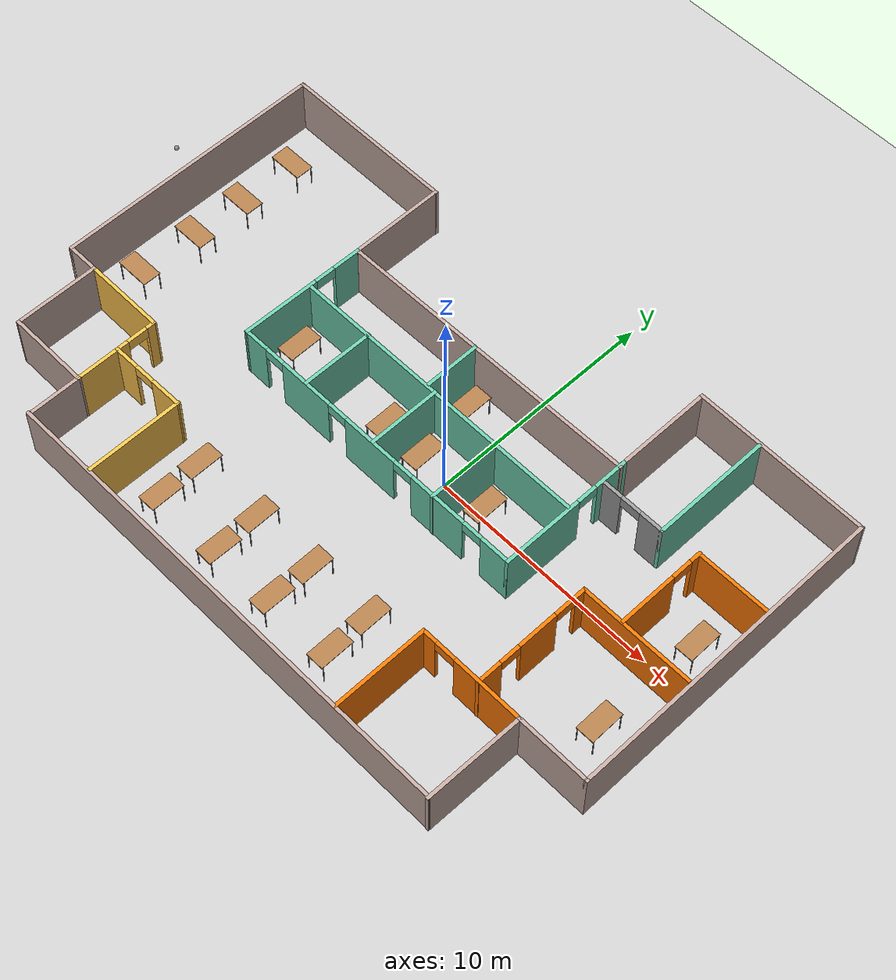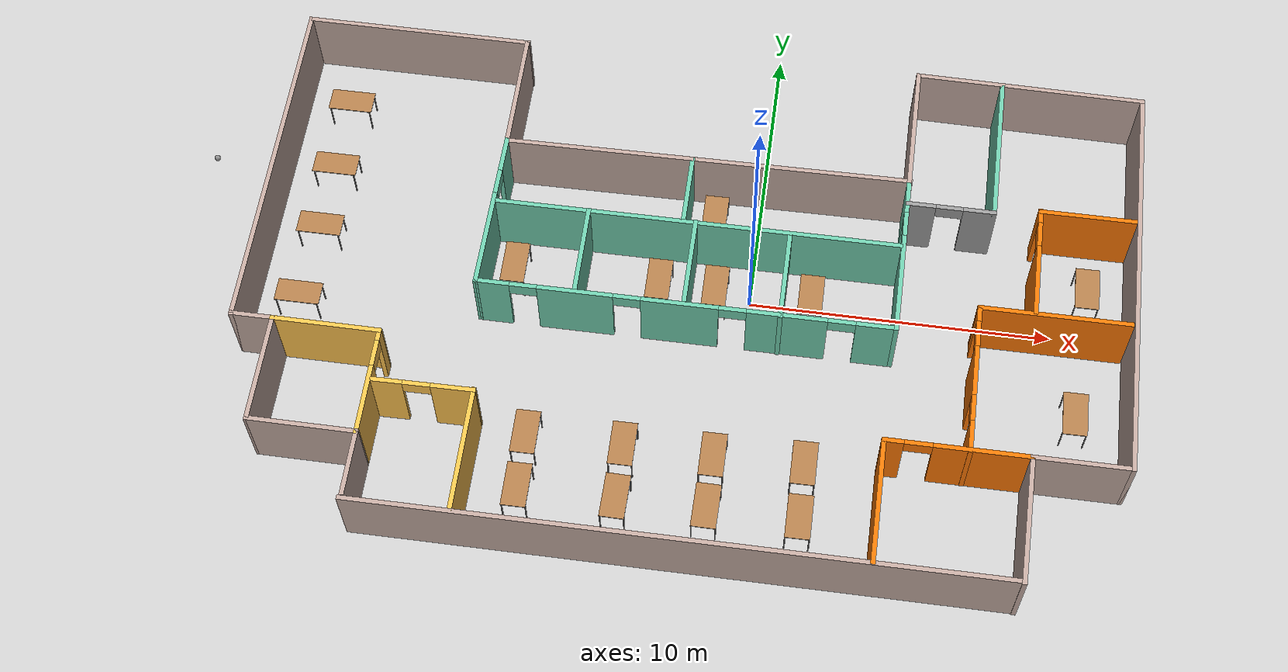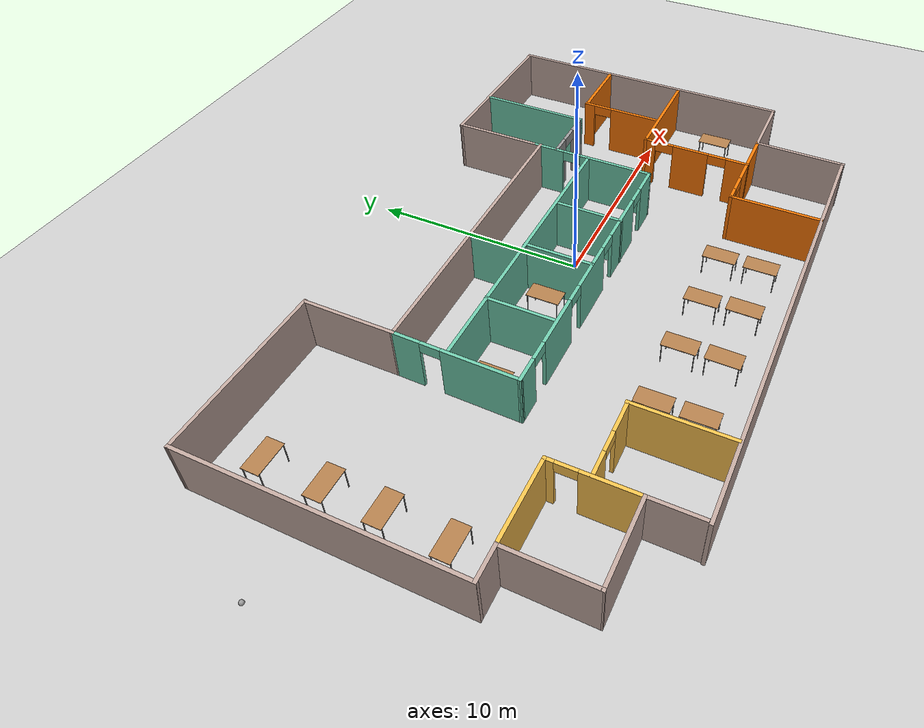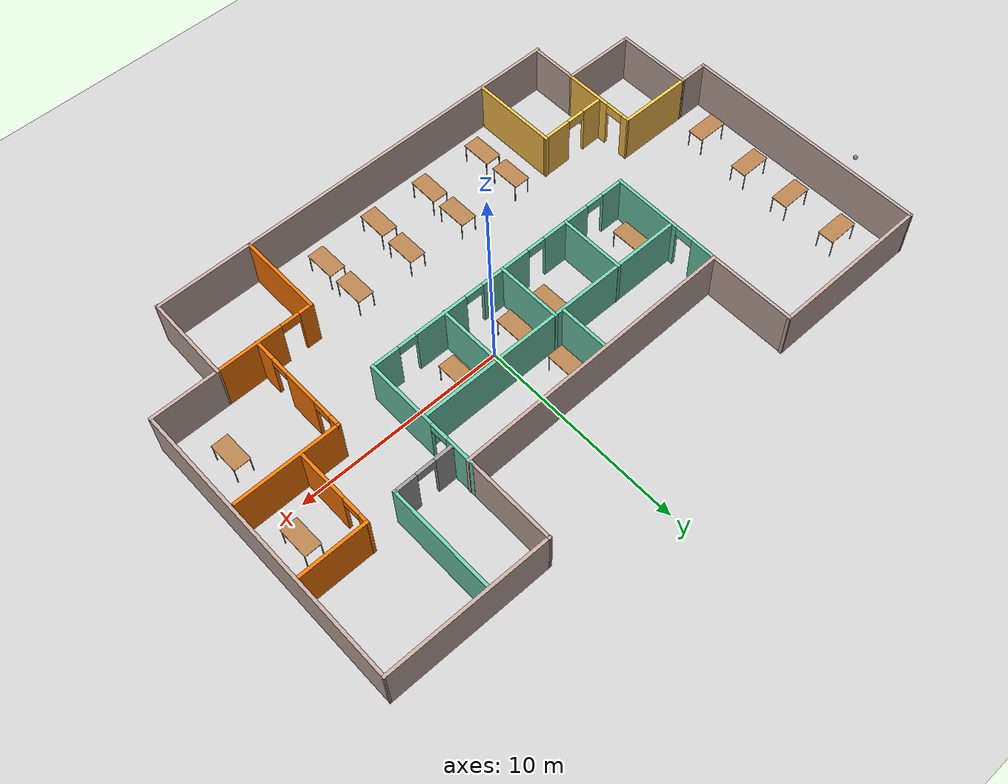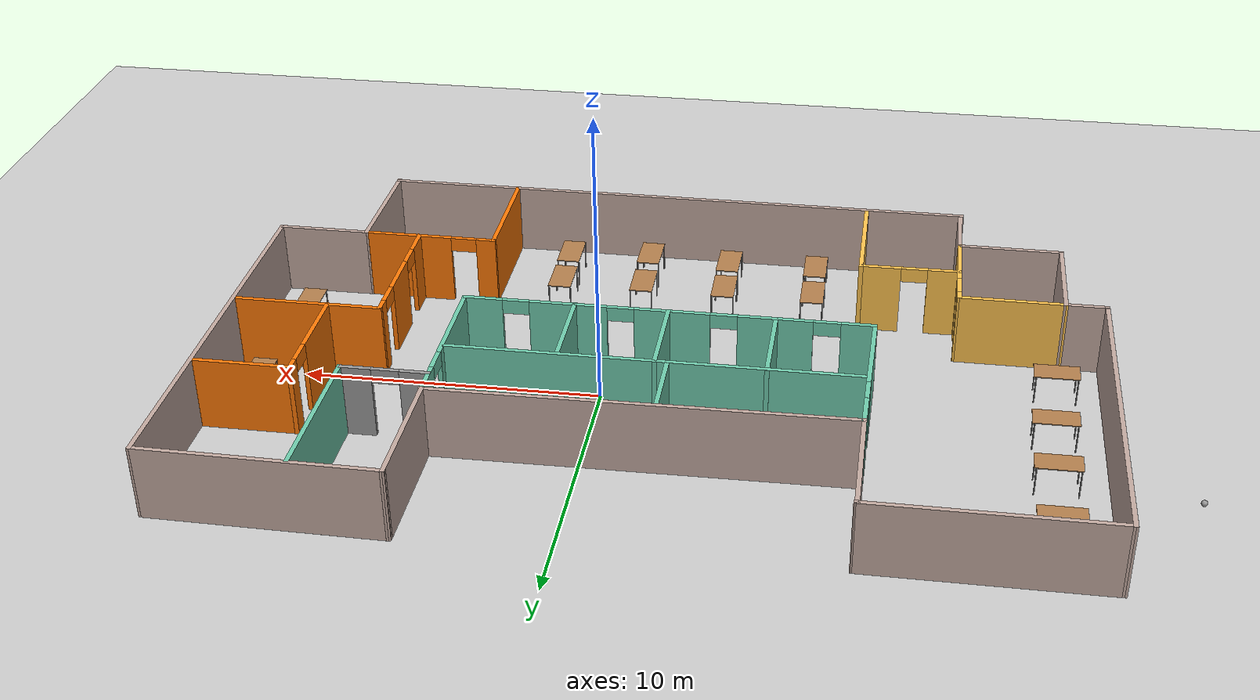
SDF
<sdf version="1.7">
 <world name="default">
  <light name="sun" type="directional">
   <pose>0 0 10 0 -0 0</pose>
   <diffuse>0.8 0.8 0.8 1</diffuse>
   <specular>0.2 0.2 0.2 1</specular>
   <attenuation>
    <range>1000</range>
    <constant>0.9</constant>
    <linear>0.01</linear>
    <quadratic>0.001</quadratic>
   </attenuation>
   <direction>-0.5 0.1 -0.9</direction>
   <spot><inner_angle>0</inner_angle><outer_angle>0</outer_angle><falloff>0</falloff></spot>
  </light>
  <model name="ground_plane">
   <static>1</static>
   <link name="link">
    <collision name="collision">
     <geometry><plane><normal>0 0 1</normal><size>100 100</size></plane></geometry>
     <surface><friction><ode><mu>100</mu><mu2>50</mu2></ode></friction></surface>
    </collision>
    <visual name="visual">
     <cast_shadows>0</cast_shadows>
     <geometry><plane><normal>0 0 1</normal><size>100 100</size></plane></geometry>
     <material>
      <script><uri>file://media/materials/scripts/gazebo.material</uri><name>Gazebo/Grey</name></script>
     </material>
    </visual>
   </link>
  </model>
  <gravity>0 0 -9.8</gravity>
  <magnetic_field>6e-06 2.3e-05 -4.2e-05</magnetic_field>
  <atmosphere type="adiabatic"/>
  <physics type="ode">
   <max_step_size>0.001</max_step_size>
   <real_time_factor>1</real_time_factor>
   <real_time_update_rate>1000</real_time_update_rate>
  </physics>
  <scene><ambient>0.4 0.4 0.4 1</ambient><background>0.7 0.7 0.7 1</background><shadows>1</shadows></scene>
  <audio><device>default</device></audio>
  <spherical_coordinates>
   <surface_model>EARTH_WGS84</surface_model>
   <latitude_deg>0</latitude_deg>
   <longitude_deg>0</longitude_deg>
   <elevation>0</elevation>
   <heading_deg>0</heading_deg>
  </spherical_coordinates>
  <model name="task_env">
   <pose>-1.95063 -0.71623 0 0 -0 0</pose>
   <link name="Wall_0">
    <collision name="Wall_0_Collision">
     <geometry><box><size>21 0.15 2.5</size></box></geometry>
     <pose>0 0 1.25 0 -0 0</pose>
    </collision>
    <visual name="Wall_0_Visual">
     <pose>0 0 1.25 0 -0 0</pose>
     <geometry><box><size>21 0.15 2.5</size></box></geometry>
     <material>
      <script><uri>file://media/materials/scripts/gazebo.material</uri><name>Gazebo/Grey</name></script>
      <ambient>0.760784 0.662745 0.627451 1</ambient>
     </material>
     <meta><layer>0</layer></meta>
    </visual>
    <pose>0.813601 -9.0219 0 0 -0 3.14159</pose>
   </link>
   <link name="Wall_14">
    <pose>-6.81536 1.8239 0 0 -0 -1.58573</pose>
    <visual name="Wall_14_Visual_0">
     <pose>-2.17991 0 1.25 0 -0 0</pose>
     <geometry><box><size>1.29492 0.15 2.5</size></box></geometry>
     <material>
      <script><uri>file://media/materials/scripts/gazebo.material</uri><name>Gazebo/Grey</name></script>
      <ambient>0.435294 0.796078 0.67451 1</ambient>
     </material>
     <meta><layer>0</layer></meta>
    </visual>
    <collision name="Wall_14_Collision_0">
     <geometry><box><size>1.29492 0.15 2.5</size></box></geometry>
     <pose>-2.17991 0 1.25 0 -0 0</pose>
    </collision>
    <visual name="Wall_14_Visual_1">
     <pose>1.09746 0 1.25 0 -0 0</pose>
     <geometry><box><size>3.45981 0.15 2.5</size></box></geometry>
     <material>
      <script><uri>file://media/materials/scripts/gazebo.material</uri><name>Gazebo/Grey</name></script>
      <ambient>0.435294 0.796078 0.67451 1</ambient>
     </material>
     <meta><layer>0</layer></meta>
    </visual>
    <collision name="Wall_14_Collision_1">
     <geometry><box><size>3.45981 0.15 2.5</size></box></geometry>
     <pose>1.09746 0 1.25 0 -0 0</pose>
    </collision>
    <visual name="Wall_14_Visual_2">
     <pose>-1.08245 0 2.25 0 -0 0</pose>
     <geometry><box><size>0.9 0.15 0.5</size></box></geometry>
     <material>
      <script><uri>file://media/materials/scripts/gazebo.material</uri><name>Gazebo/Grey</name></script>
      <ambient>0.435294 0.796078 0.67451 1</ambient>
     </material>
     <meta><layer>0</layer></meta>
    </visual>
    <collision name="Wall_14_Collision_2">
     <geometry><box><size>0.9 0.15 0.5</size></box></geometry>
     <pose>-1.08245 0 2.25 0 -0 0</pose>
    </collision>
   </link>
   <link name="Wall_15">
    <pose>-0.056466 -0.928165 0 0 -0 0</pose>
    <visual name="Wall_15_Visual_0">
     <pose>-6.28596 0 1.25 0 -0 0</pose>
     <geometry><box><size>1.17807 0.15 2.5</size></box></geometry>
     <material>
      <script><uri>file://media/materials/scripts/gazebo.material</uri><name>Gazebo/Grey</name></script>
      <ambient>0.435294 0.796078 0.67451 1</ambient>
     </material>
     <meta><layer>0</layer></meta>
    </visual>
    <collision name="Wall_15_Collision_0">
     <geometry><box><size>1.17807 0.15 2.5</size></box></geometry>
     <pose>-6.28596 0 1.25 0 -0 0</pose>
    </collision>
    <visual name="Wall_15_Visual_1">
     <pose>-3.55454 0 1.25 0 -0 0</pose>
     <geometry><box><size>2.48478 0.15 2.5</size></box></geometry>
     <material>
      <script><uri>file://media/materials/scripts/gazebo.material</uri><name>Gazebo/Grey</name></script>
      <ambient>0.435294 0.796078 0.67451 1</ambient>
     </material>
     <meta><layer>0</layer></meta>
    </visual>
    <collision name="Wall_15_Collision_1">
     <geometry><box><size>2.48478 0.15 2.5</size></box></geometry>
     <pose>-3.55454 0 1.25 0 -0 0</pose>
    </collision>
    <visual name="Wall_15_Visual_2">
     <pose>-0.146887 0 1.25 0 -0 0</pose>
     <geometry><box><size>2.53052 0.15 2.5</size></box></geometry>
     <material>
      <script><uri>file://media/materials/scripts/gazebo.material</uri><name>Gazebo/Grey</name></script>
      <ambient>0.435294 0.796078 0.67451 1</ambient>
     </material>
     <meta><layer>0</layer></meta>
    </visual>
    <collision name="Wall_15_Collision_2">
     <geometry><box><size>2.53052 0.15 2.5</size></box></geometry>
     <pose>-0.146887 0 1.25 0 -0 0</pose>
    </collision>
    <visual name="Wall_15_Visual_3">
     <pose>3.32937 0 1.25 0 -0 0</pose>
     <geometry><box><size>2.622 0.15 2.5</size></box></geometry>
     <material>
      <script><uri>file://media/materials/scripts/gazebo.material</uri><name>Gazebo/Grey</name></script>
      <ambient>0.435294 0.796078 0.67451 1</ambient>
     </material>
     <meta><layer>0</layer></meta>
    </visual>
    <collision name="Wall_15_Collision_3">
     <geometry><box><size>2.622 0.15 2.5</size></box></geometry>
     <pose>3.32937 0 1.25 0 -0 0</pose>
    </collision>
    <visual name="Wall_15_Visual_4">
     <pose>6.20769 0 1.25 0 -0 0</pose>
     <geometry><box><size>1.33463 0.15 2.5</size></box></geometry>
     <material>
      <script><uri>file://media/materials/scripts/gazebo.material</uri><name>Gazebo/Grey</name></script>
      <ambient>0.435294 0.796078 0.67451 1</ambient>
     </material>
     <meta><layer>0</layer></meta>
    </visual>
    <collision name="Wall_15_Collision_4">
     <geometry><box><size>1.33463 0.15 2.5</size></box></geometry>
     <pose>6.20769 0 1.25 0 -0 0</pose>
    </collision>
    <visual name="Wall_15_Visual_5">
     <pose>-5.24693 0 2.25 0 -0 0</pose>
     <geometry><box><size>0.9 0.15 0.5</size></box></geometry>
     <material>
      <script><uri>file://media/materials/scripts/gazebo.material</uri><name>Gazebo/Grey</name></script>
      <ambient>0.435294 0.796078 0.67451 1</ambient>
     </material>
     <meta><layer>0</layer></meta>
    </visual>
    <collision name="Wall_15_Collision_5">
     <geometry><box><size>0.9 0.15 0.5</size></box></geometry>
     <pose>-5.24693 0 2.25 0 -0 0</pose>
    </collision>
    <visual name="Wall_15_Visual_6">
     <pose>-1.86215 0 2.25 0 -0 0</pose>
     <geometry><box><size>0.9 0.15 0.5</size></box></geometry>
     <material>
      <script><uri>file://media/materials/scripts/gazebo.material</uri><name>Gazebo/Grey</name></script>
      <ambient>0.435294 0.796078 0.67451 1</ambient>
     </material>
     <meta><layer>0</layer></meta>
    </visual>
    <collision name="Wall_15_Collision_6">
     <geometry><box><size>0.9 0.15 0.5</size></box></geometry>
     <pose>-1.86215 0 2.25 0 -0 0</pose>
    </collision>
    <visual name="Wall_15_Visual_7">
     <pose>1.56837 0 2.25 0 -0 0</pose>
     <geometry><box><size>0.9 0.15 0.5</size></box></geometry>
     <material>
      <script><uri>file://media/materials/scripts/gazebo.material</uri><name>Gazebo/Grey</name></script>
      <ambient>0.435294 0.796078 0.67451 1</ambient>
     </material>
     <meta><layer>0</layer></meta>
    </visual>
    <collision name="Wall_15_Collision_7">
     <geometry><box><size>0.9 0.15 0.5</size></box></geometry>
     <pose>1.56837 0 2.25 0 -0 0</pose>
    </collision>
    <visual name="Wall_15_Visual_8">
     <pose>5.09037 0 2.25 0 -0 0</pose>
     <geometry><box><size>0.9 0.15 0.5</size></box></geometry>
     <material>
      <script><uri>file://media/materials/scripts/gazebo.material</uri><name>Gazebo/Grey</name></script>
      <ambient>0.435294 0.796078 0.67451 1</ambient>
     </material>
     <meta><layer>0</layer></meta>
    </visual>
    <collision name="Wall_15_Collision_8">
     <geometry><box><size>0.9 0.15 0.5</size></box></geometry>
     <pose>5.09037 0 2.25 0 -0 0</pose>
    </collision>
   </link>
   <link name="Wall_16">
    <pose>6.77412 1.99683 0 0 -0 1.5708</pose>
    <visual name="Wall_16_Visual_0">
     <pose>-1.2114 0 1.25 0 -0 0</pose>
     <geometry><box><size>3.57719 0.15 2.5</size></box></geometry>
     <material>
      <script><uri>file://media/materials/scripts/gazebo.material</uri><name>Gazebo/Grey</name></script>
      <ambient>0.435294 0.796078 0.67451 1</ambient>
     </material>
     <meta><layer>0</layer></meta>
    </visual>
    <collision name="Wall_16_Collision_0">
     <geometry><box><size>3.57719 0.15 2.5</size></box></geometry>
     <pose>-1.2114 0 1.25 0 -0 0</pose>
    </collision>
    <visual name="Wall_16_Visual_1">
     <pose>2.2386 0 1.25 0 -0 0</pose>
     <geometry><box><size>1.52281 0.15 2.5</size></box></geometry>
     <material>
      <script><uri>file://media/materials/scripts/gazebo.material</uri><name>Gazebo/Grey</name></script>
      <ambient>0.435294 0.796078 0.67451 1</ambient>
     </material>
     <meta><layer>0</layer></meta>
    </visual>
    <collision name="Wall_16_Collision_1">
     <geometry><box><size>1.52281 0.15 2.5</size></box></geometry>
     <pose>2.2386 0 1.25 0 -0 0</pose>
    </collision>
    <visual name="Wall_16_Visual_2">
     <pose>1.02719 0 2.25 0 -0 0</pose>
     <geometry><box><size>0.9 0.15 0.5</size></box></geometry>
     <material>
      <script><uri>file://media/materials/scripts/gazebo.material</uri><name>Gazebo/Grey</name></script>
      <ambient>0.435294 0.796078 0.67451 1</ambient>
     </material>
     <meta><layer>0</layer></meta>
    </visual>
    <collision name="Wall_16_Collision_2">
     <geometry><box><size>0.9 0.15 0.5</size></box></geometry>
     <pose>1.02719 0 2.25 0 -0 0</pose>
    </collision>
   </link>
   <link name="Wall_18">
    <collision name="Wall_18_Collision">
     <geometry><box><size>13.5 0.15 2.5</size></box></geometry>
     <pose>0 0 1.25 0 -0 0</pose>
    </collision>
    <visual name="Wall_18_Visual">
     <pose>0 0 1.25 0 -0 0</pose>
     <geometry><box><size>13.5 0.15 2.5</size></box></geometry>
     <material>
      <script><uri>file://media/materials/scripts/gazebo.material</uri><name>Gazebo/Grey</name></script>
      <ambient>0.435294 0.796078 0.67451 1</ambient>
     </material>
     <meta><layer>0</layer></meta>
    </visual>
    <pose>-0.003534 2.1603 0 0 -0 0</pose>
   </link>
   <link name="Wall_2">
    <collision name="Wall_2_Collision">
     <geometry><box><size>4.30502 0.15 2.5</size></box></geometry>
     <pose>0 0 1.25 0 -0 0</pose>
    </collision>
    <visual name="Wall_2_Visual">
     <pose>0 0 1.25 0 -0 0</pose>
     <geometry><box><size>4.30502 0.15 2.5</size></box></geometry>
     <material>
      <script><uri>file://media/materials/scripts/gazebo.material</uri><name>Gazebo/Grey</name></script>
      <ambient>0.760784 0.662745 0.627451 1</ambient>
     </material>
     <meta><layer>0</layer></meta>
    </visual>
    <pose>11.269 -6.97503 0 0 -0 1.55615</pose>
   </link>
   <link name="Wall_20">
    <collision name="Wall_20_Collision">
     <geometry><box><size>2.5 0.15 2.5</size></box></geometry>
     <pose>0 0 1.25 0 -0 0</pose>
    </collision>
    <visual name="Wall_20_Visual">
     <pose>0 0 1.25 0 -0 0</pose>
     <geometry><box><size>2.5 0.15 2.5</size></box></geometry>
     <material>
      <script><uri>file://media/materials/scripts/gazebo.material</uri><name>Gazebo/Grey</name></script>
      <ambient>0.435294 0.796078 0.67451 1</ambient>
     </material>
     <meta><layer>0</layer></meta>
    </visual>
    <pose>-0.484987 3.44269 0 0 -0 -1.5708</pose>
   </link>
   <link name="Wall_22">
    <collision name="Wall_22_Collision">
     <geometry><box><size>3.25 0.15 2.5</size></box></geometry>
     <pose>0 0 1.25 0 -0 0</pose>
    </collision>
    <visual name="Wall_22_Visual">
     <pose>0 0 1.25 0 -0 0</pose>
     <geometry><box><size>3.25 0.15 2.5</size></box></geometry>
     <material>
      <script><uri>file://media/materials/scripts/gazebo.material</uri><name>Gazebo/Grey</name></script>
      <ambient>0.435294 0.796078 0.67451 1</ambient>
     </material>
     <meta><layer>0</layer></meta>
    </visual>
    <pose>-3.62724 0.626735 0 0 -0 -1.5708</pose>
   </link>
   <link name="Wall_26">
    <collision name="Wall_26_Collision">
     <geometry><box><size>3.25 0.15 2.5</size></box></geometry>
     <pose>0 0 1.25 0 -0 0</pose>
    </collision>
    <visual name="Wall_26_Visual">
     <pose>0 0 1.25 0 -0 0</pose>
     <geometry><box><size>3.25 0.15 2.5</size></box></geometry>
     <material>
      <script><uri>file://media/materials/scripts/gazebo.material</uri><name>Gazebo/Grey</name></script>
      <ambient>0.435294 0.796078 0.67451 1</ambient>
     </material>
     <meta><layer>0</layer></meta>
    </visual>
    <pose>3.05396 0.591755 0 0 -0 -1.5708</pose>
   </link>
   <link name="Wall_28">
    <collision name="Wall_28_Collision">
     <geometry><box><size>3.25 0.15 2.5</size></box></geometry>
     <pose>0 0 1.25 0 -0 0</pose>
    </collision>
    <visual name="Wall_28_Visual">
     <pose>0 0 1.25 0 -0 0</pose>
     <geometry><box><size>3.25 0.15 2.5</size></box></geometry>
     <material>
      <script><uri>file://media/materials/scripts/gazebo.material</uri><name>Gazebo/Grey</name></script>
      <ambient>0.435294 0.796078 0.67451 1</ambient>
     </material>
     <meta><layer>0</layer></meta>
    </visual>
    <pose>-0.072747 0.627413 0 0 -0 -1.5708</pose>
   </link>
   <link name="Wall_3">
    <collision name="Wall_3_Collision">
     <geometry><box><size>3.25 0.15 2.5</size></box></geometry>
     <pose>0 0 1.25 0 -0 0</pose>
    </collision>
    <visual name="Wall_3_Visual">
     <pose>0 0 1.25 0 -0 0</pose>
     <geometry><box><size>3.25 0.15 2.5</size></box></geometry>
     <material>
      <script><uri>file://media/materials/scripts/gazebo.material</uri><name>Gazebo/Grey</name></script>
      <ambient>0.760784 0.662745 0.627451 1</ambient>
     </material>
     <meta><layer>0</layer></meta>
    </visual>
    <pose>12.8494 -4.89774 0 0 -0 0</pose>
   </link>
   <link name="Wall_30">
    <pose>8.21532 3.82761 0 0 -0 0</pose>
    <visual name="Wall_30_Visual_0">
     <pose>-0.999101 0 1.25 0 -0 0</pose>
     <geometry><box><size>1.0018 0.15 2.5</size></box></geometry>
     <material>
      <script><uri>file://media/materials/scripts/gazebo.material</uri><name>Gazebo/Grey</name></script>
      <ambient>1 1 1 1</ambient>
     </material>
     <meta><layer>0</layer></meta>
    </visual>
    <collision name="Wall_30_Collision_0">
     <geometry><box><size>1.0018 0.15 2.5</size></box></geometry>
     <pose>-0.999101 0 1.25 0 -0 0</pose>
    </collision>
    <visual name="Wall_30_Visual_1">
     <pose>0.950899 0 1.25 0 -0 0</pose>
     <geometry><box><size>1.0982 0.15 2.5</size></box></geometry>
     <material>
      <script><uri>file://media/materials/scripts/gazebo.material</uri><name>Gazebo/Grey</name></script>
      <ambient>1 1 1 1</ambient>
     </material>
     <meta><layer>0</layer></meta>
    </visual>
    <collision name="Wall_30_Collision_1">
     <geometry><box><size>1.0982 0.15 2.5</size></box></geometry>
     <pose>0.950899 0 1.25 0 -0 0</pose>
    </collision>
    <visual name="Wall_30_Visual_2">
     <pose>-0.048203 0 2.25 0 -0 0</pose>
     <geometry><box><size>0.9 0.15 0.5</size></box></geometry>
     <material>
      <script><uri>file://media/materials/scripts/gazebo.material</uri><name>Gazebo/Grey</name></script>
      <ambient>1 1 1 1</ambient>
     </material>
     <meta><layer>0</layer></meta>
    </visual>
    <collision name="Wall_30_Collision_2">
     <geometry><box><size>0.9 0.15 0.5</size></box></geometry>
     <pose>-0.048203 0 2.25 0 -0 0</pose>
    </collision>
   </link>
   <link name="Wall_31">
    <collision name="Wall_31_Collision">
     <geometry><box><size>5.25 0.15 2.5</size></box></geometry>
     <pose>0 0 1.25 0 -0 0</pose>
    </collision>
    <visual name="Wall_31_Visual">
     <pose>0 0 1.25 0 -0 0</pose>
     <geometry><box><size>5.25 0.15 2.5</size></box></geometry>
     <material>
      <script><uri>file://media/materials/scripts/gazebo.material</uri><name>Gazebo/Grey</name></script>
      <ambient>0.435294 0.796078 0.67451 1</ambient>
     </material>
     <meta><layer>0</layer></meta>
    </visual>
    <pose>9.64032 6.37761 0 0 -0 1.5708</pose>
   </link>
   <link name="Wall_33">
    <pose>-7.87138 -4.88643 0 0 -0 0.010314</pose>
    <visual name="Wall_33_Visual_0">
     <pose>-1.17411 0 1.25 0 -0 0</pose>
     <geometry><box><size>1.1406 0.15 2.5</size></box></geometry>
     <material>
      <script><uri>file://media/materials/scripts/gazebo.material</uri><name>Gazebo/Grey</name></script>
      <ambient>1 0.764706 0.305882 1</ambient>
     </material>
     <meta><layer>0</layer></meta>
    </visual>
    <collision name="Wall_33_Collision_0">
     <geometry><box><size>1.1406 0.15 2.5</size></box></geometry>
     <pose>-1.17411 0 1.25 0 -0 0</pose>
    </collision>
    <visual name="Wall_33_Visual_1">
     <pose>1.0203 0 1.25 0 -0 0</pose>
     <geometry><box><size>1.44823 0.15 2.5</size></box></geometry>
     <material>
      <script><uri>file://media/materials/scripts/gazebo.material</uri><name>Gazebo/Grey</name></script>
      <ambient>1 0.764706 0.305882 1</ambient>
     </material>
     <meta><layer>0</layer></meta>
    </visual>
    <collision name="Wall_33_Collision_1">
     <geometry><box><size>1.44823 0.15 2.5</size></box></geometry>
     <pose>1.0203 0 1.25 0 -0 0</pose>
    </collision>
    <visual name="Wall_33_Visual_2">
     <pose>-0.153815 0 2.25 0 -0 0</pose>
     <geometry><box><size>0.9 0.15 0.5</size></box></geometry>
     <material>
      <script><uri>file://media/materials/scripts/gazebo.material</uri><name>Gazebo/Grey</name></script>
      <ambient>1 0.764706 0.305882 1</ambient>
     </material>
     <meta><layer>0</layer></meta>
    </visual>
    <collision name="Wall_33_Collision_2">
     <geometry><box><size>0.9 0.15 0.5</size></box></geometry>
     <pose>-0.153815 0 2.25 0 -0 0</pose>
    </collision>
   </link>
   <link name="Wall_34">
    <collision name="Wall_34_Collision">
     <geometry><box><size>4.25 0.15 2.5</size></box></geometry>
     <pose>0 0 1.25 0 -0 0</pose>
    </collision>
    <visual name="Wall_34_Visual">
     <pose>0 0 1.25 0 -0 0</pose>
     <geometry><box><size>4.25 0.15 2.5</size></box></geometry>
     <material>
      <script><uri>file://media/materials/scripts/gazebo.material</uri><name>Gazebo/Grey</name></script>
      <ambient>1 0.764706 0.305882 1</ambient>
     </material>
     <meta><layer>0</layer></meta>
    </visual>
    <pose>-6.20205 -6.89932 0 0 -0 -1.5708</pose>
   </link>
   <link name="Wall_36">
    <pose>8.99944 -4.89774 0 0 -0 3.14159</pose>
    <visual name="Wall_36_Visual_0">
     <pose>-0.798861 0 1.25 0 -0 0</pose>
     <geometry><box><size>3.15228 0.15 2.5</size></box></geometry>
     <material>
      <script><uri>file://media/materials/scripts/gazebo.material</uri><name>Gazebo/Grey</name></script>
      <ambient>0.996078 0.47451 0.0196078 1</ambient>
     </material>
     <meta><layer>0</layer></meta>
    </visual>
    <collision name="Wall_36_Collision_0">
     <geometry><box><size>3.15228 0.15 2.5</size></box></geometry>
     <pose>-0.798861 0 1.25 0 -0 0</pose>
    </collision>
    <visual name="Wall_36_Visual_1">
     <pose>2.02614 0 1.25 0 -0 0</pose>
     <geometry><box><size>0.697723 0.15 2.5</size></box></geometry>
     <material>
      <script><uri>file://media/materials/scripts/gazebo.material</uri><name>Gazebo/Grey</name></script>
      <ambient>0.996078 0.47451 0.0196078 1</ambient>
     </material>
     <meta><layer>0</layer></meta>
    </visual>
    <collision name="Wall_36_Collision_1">
     <geometry><box><size>0.697723 0.15 2.5</size></box></geometry>
     <pose>2.02614 0 1.25 0 -0 0</pose>
    </collision>
    <visual name="Wall_36_Visual_2">
     <pose>1.22728 0 2.25 0 -0 0</pose>
     <geometry><box><size>0.9 0.15 0.5</size></box></geometry>
     <material>
      <script><uri>file://media/materials/scripts/gazebo.material</uri><name>Gazebo/Grey</name></script>
      <ambient>0.996078 0.47451 0.0196078 1</ambient>
     </material>
     <meta><layer>0</layer></meta>
    </visual>
    <collision name="Wall_36_Collision_2">
     <geometry><box><size>0.9 0.15 0.5</size></box></geometry>
     <pose>1.22728 0 2.25 0 -0 0</pose>
    </collision>
   </link>
   <link name="Wall_37">
    <collision name="Wall_37_Collision">
     <geometry><box><size>4.25 0.15 2.5</size></box></geometry>
     <pose>0 0 1.25 0 -0 0</pose>
    </collision>
    <visual name="Wall_37_Visual">
     <pose>0 0 1.25 0 -0 0</pose>
     <geometry><box><size>4.25 0.15 2.5</size></box></geometry>
     <material>
      <script><uri>file://media/materials/scripts/gazebo.material</uri><name>Gazebo/Grey</name></script>
      <ambient>0.996078 0.47451 0.0196078 1</ambient>
     </material>
     <meta><layer>0</layer></meta>
    </visual>
    <pose>6.69944 -6.94774 0 0 -0 -1.5708</pose>
   </link>
   <link name="Wall_39">
    <pose>9.37843 -2.36401 0 0 -0 1.5708</pose>
    <visual name="Wall_39_Visual_0">
     <pose>-2.07103 0 1.25 0 -0 0</pose>
     <geometry><box><size>1.10794 0.15 2.5</size></box></geometry>
     <material>
      <script><uri>file://media/materials/scripts/gazebo.material</uri><name>Gazebo/Grey</name></script>
      <ambient>0.996078 0.47451 0.0196078 1</ambient>
     </material>
     <meta><layer>0</layer></meta>
    </visual>
    <collision name="Wall_39_Collision_0">
     <geometry><box><size>1.10794 0.15 2.5</size></box></geometry>
     <pose>-2.07103 0 1.25 0 -0 0</pose>
    </collision>
    <visual name="Wall_39_Visual_1">
     <pose>0.261125 0 1.25 0 -0 0</pose>
     <geometry><box><size>1.75636 0.15 2.5</size></box></geometry>
     <material>
      <script><uri>file://media/materials/scripts/gazebo.material</uri><name>Gazebo/Grey</name></script>
      <ambient>0.996078 0.47451 0.0196078 1</ambient>
     </material>
     <meta><layer>0</layer></meta>
    </visual>
    <collision name="Wall_39_Collision_1">
     <geometry><box><size>1.75636 0.15 2.5</size></box></geometry>
     <pose>0.261125 0 1.25 0 -0 0</pose>
    </collision>
    <visual name="Wall_39_Visual_2">
     <pose>2.33215 0 1.25 0 -0 0</pose>
     <geometry><box><size>0.585692 0.15 2.5</size></box></geometry>
     <material>
      <script><uri>file://media/materials/scripts/gazebo.material</uri><name>Gazebo/Grey</name></script>
      <ambient>0.996078 0.47451 0.0196078 1</ambient>
     </material>
     <meta><layer>0</layer></meta>
    </visual>
    <collision name="Wall_39_Collision_2">
     <geometry><box><size>0.585692 0.15 2.5</size></box></geometry>
     <pose>2.33215 0 1.25 0 -0 0</pose>
    </collision>
    <visual name="Wall_39_Visual_3">
     <pose>-1.06706 0 2.25 0 -0 0</pose>
     <geometry><box><size>0.9 0.15 0.5</size></box></geometry>
     <material>
      <script><uri>file://media/materials/scripts/gazebo.material</uri><name>Gazebo/Grey</name></script>
      <ambient>0.996078 0.47451 0.0196078 1</ambient>
     </material>
     <meta><layer>0</layer></meta>
    </visual>
    <collision name="Wall_39_Collision_3">
     <geometry><box><size>0.9 0.15 0.5</size></box></geometry>
     <pose>-1.06706 0 2.25 0 -0 0</pose>
    </collision>
    <visual name="Wall_39_Visual_4">
     <pose>1.58931 0 2.25 0 -0 0</pose>
     <geometry><box><size>0.9 0.15 0.5</size></box></geometry>
     <material>
      <script><uri>file://media/materials/scripts/gazebo.material</uri><name>Gazebo/Grey</name></script>
      <ambient>0.996078 0.47451 0.0196078 1</ambient>
     </material>
     <meta><layer>0</layer></meta>
    </visual>
    <collision name="Wall_39_Collision_4">
     <geometry><box><size>0.9 0.15 0.5</size></box></geometry>
     <pose>1.58931 0 2.25 0 -0 0</pose>
    </collision>
   </link>
   <link name="Wall_4">
    <collision name="Wall_4_Collision">
     <geometry><box><size>14 0.15 2.5</size></box></geometry>
     <pose>0 0 1.25 0 -0 0</pose>
    </collision>
    <visual name="Wall_4_Visual">
     <pose>0 0 1.25 0 -0 0</pose>
     <geometry><box><size>14 0.15 2.5</size></box></geometry>
     <material>
      <script><uri>file://media/materials/scripts/gazebo.material</uri><name>Gazebo/Grey</name></script>
      <ambient>0.760784 0.662745 0.627451 1</ambient>
     </material>
     <meta><layer>0</layer></meta>
    </visual>
    <pose>14.3994 2.02726 0 0 -0 1.5708</pose>
   </link>
   <link name="Wall_40">
    <collision name="Wall_40_Collision">
     <geometry><box><size>5 0.15 2.5</size></box></geometry>
     <pose>0 0 1.25 0 -0 0</pose>
    </collision>
    <visual name="Wall_40_Visual">
     <pose>0 0 1.25 0 -0 0</pose>
     <geometry><box><size>5 0.15 2.5</size></box></geometry>
     <material>
      <script><uri>file://media/materials/scripts/gazebo.material</uri><name>Gazebo/Grey</name></script>
      <ambient>0.996078 0.47451 0.0196078 1</ambient>
     </material>
     <meta><layer>0</layer></meta>
    </visual>
    <pose>11.8034 0.185989 0 0 -0 0</pose>
   </link>
   <link name="Wall_42">
    <pose>11.164 2.16814 0 0 -0 1.5708</pose>
    <visual name="Wall_42_Visual_0">
     <pose>-0.710725 0 1.25 0 -0 0</pose>
     <geometry><box><size>2.57855 0.15 2.5</size></box></geometry>
     <material>
      <script><uri>file://media/materials/scripts/gazebo.material</uri><name>Gazebo/Grey</name></script>
      <ambient>0.996078 0.47451 0.0196078 1</ambient>
     </material>
     <meta><layer>0</layer></meta>
    </visual>
    <collision name="Wall_42_Collision_0">
     <geometry><box><size>2.57855 0.15 2.5</size></box></geometry>
     <pose>-0.710725 0 1.25 0 -0 0</pose>
    </collision>
    <visual name="Wall_42_Visual_1">
     <pose>1.73927 0 1.25 0 -0 0</pose>
     <geometry><box><size>0.52145 0.15 2.5</size></box></geometry>
     <material>
      <script><uri>file://media/materials/scripts/gazebo.material</uri><name>Gazebo/Grey</name></script>
      <ambient>0.996078 0.47451 0.0196078 1</ambient>
     </material>
     <meta><layer>0</layer></meta>
    </visual>
    <collision name="Wall_42_Collision_1">
     <geometry><box><size>0.52145 0.15 2.5</size></box></geometry>
     <pose>1.73927 0 1.25 0 -0 0</pose>
    </collision>
    <visual name="Wall_42_Visual_2">
     <pose>1.02855 0 2.25 0 -0 0</pose>
     <geometry><box><size>0.9 0.15 0.5</size></box></geometry>
     <material>
      <script><uri>file://media/materials/scripts/gazebo.material</uri><name>Gazebo/Grey</name></script>
      <ambient>0.996078 0.47451 0.0196078 1</ambient>
     </material>
     <meta><layer>0</layer></meta>
    </visual>
    <collision name="Wall_42_Collision_2">
     <geometry><box><size>0.9 0.15 0.5</size></box></geometry>
     <pose>1.02855 0 2.25 0 -0 0</pose>
    </collision>
   </link>
   <link name="Wall_43">
    <collision name="Wall_43_Collision">
     <geometry><box><size>3.25 0.15 2.5</size></box></geometry>
     <pose>0 0 1.25 0 -0 0</pose>
    </collision>
    <visual name="Wall_43_Visual">
     <pose>0 0 1.25 0 -0 0</pose>
     <geometry><box><size>3.25 0.15 2.5</size></box></geometry>
     <material>
      <script><uri>file://media/materials/scripts/gazebo.material</uri><name>Gazebo/Grey</name></script>
      <ambient>0.996078 0.47451 0.0196078 1</ambient>
     </material>
     <meta><layer>0</layer></meta>
    </visual>
    <pose>12.714 4.07811 0 0 -0 0</pose>
   </link>
   <link name="Wall_45">
    <collision name="Wall_45_Collision">
     <geometry><box><size>3.64292 0.15 2.5</size></box></geometry>
     <pose>0 0 1.25 0 -0 0</pose>
    </collision>
    <visual name="Wall_45_Visual">
     <pose>0 0 1.25 0 -0 0</pose>
     <geometry><box><size>3.64292 0.15 2.5</size></box></geometry>
     <material>
      <script><uri>file://media/materials/scripts/gazebo.material</uri><name>Gazebo/Grey</name></script>
      <ambient>0.760784 0.662745 0.627451 1</ambient>
     </material>
     <meta><layer>0</layer></meta>
    </visual>
    <pose>-11.3041 -6.75408 0 0 -0 3.13796</pose>
   </link>
   <link name="Wall_46">
    <collision name="Wall_46_Collision">
     <geometry><box><size>3.75 0.15 2.5</size></box></geometry>
     <pose>0 0 1.25 0 -0 0</pose>
    </collision>
    <visual name="Wall_46_Visual">
     <pose>0 0 1.25 0 -0 0</pose>
     <geometry><box><size>3.75 0.15 2.5</size></box></geometry>
     <material>
      <script><uri>file://media/materials/scripts/gazebo.material</uri><name>Gazebo/Grey</name></script>
      <ambient>0.760784 0.662745 0.627451 1</ambient>
     </material>
     <meta><layer>0</layer></meta>
    </visual>
    <pose>-13.0506 -4.94774 0 0 -0 1.5708</pose>
   </link>
   <link name="Wall_5">
    <collision name="Wall_5_Collision">
     <geometry><box><size>7.78206 0.15 2.5</size></box></geometry>
     <pose>0 0 1.25 0 -0 0</pose>
    </collision>
    <visual name="Wall_5_Visual">
     <pose>0 0 1.25 0 -0 0</pose>
     <geometry><box><size>7.78206 0.15 2.5</size></box></geometry>
     <material>
      <script><uri>file://media/materials/scripts/gazebo.material</uri><name>Gazebo/Grey</name></script>
      <ambient>0.760784 0.662745 0.627451 1</ambient>
     </material>
     <meta><layer>0</layer></meta>
    </visual>
    <pose>10.5841 9.00234 0 0 -0 3.12847</pose>
   </link>
   <link name="Wall_50">
    <collision name="Wall_50_Collision">
     <geometry><box><size>12 0.15 2.5</size></box></geometry>
     <pose>0 0 1.25 0 -0 0</pose>
    </collision>
    <visual name="Wall_50_Visual">
     <pose>0 0 1.25 0 -0 0</pose>
     <geometry><box><size>12 0.15 2.5</size></box></geometry>
     <material>
      <script><uri>file://media/materials/scripts/gazebo.material</uri><name>Gazebo/Grey</name></script>
      <ambient>0.760784 0.662745 0.627451 1</ambient>
     </material>
     <meta><layer>0</layer></meta>
    </visual>
    <pose>-14.4006 2.77726 0 0 -0 -1.5708</pose>
   </link>
   <link name="Wall_52">
    <collision name="Wall_52_Collision">
     <geometry><box><size>1.5 0.15 2.5</size></box></geometry>
     <pose>0 0 1.25 0 -0 0</pose>
    </collision>
    <visual name="Wall_52_Visual">
     <pose>0 0 1.25 0 -0 0</pose>
     <geometry><box><size>1.5 0.15 2.5</size></box></geometry>
     <material>
      <script><uri>file://media/materials/scripts/gazebo.material</uri><name>Gazebo/Grey</name></script>
      <ambient>0.760784 0.662745 0.627451 1</ambient>
     </material>
     <meta><layer>0</layer></meta>
    </visual>
    <pose>-13.7256 -3.14774 0 0 -0 0</pose>
   </link>
   <link name="Wall_54">
    <collision name="Wall_54_Collision">
     <geometry><box><size>3.64292 0.15 2.5</size></box></geometry>
     <pose>0 0 1.25 0 -0 0</pose>
    </collision>
    <visual name="Wall_54_Visual">
     <pose>0 0 1.25 0 -0 0</pose>
     <geometry><box><size>3.64292 0.15 2.5</size></box></geometry>
     <material>
      <script><uri>file://media/materials/scripts/gazebo.material</uri><name>Gazebo/Grey</name></script>
      <ambient>1 0.764706 0.305882 1</ambient>
     </material>
     <meta><layer>0</layer></meta>
    </visual>
    <pose>-11.3041 -3.15408 0 0 -0 -0.003628</pose>
   </link>
   <link name="Wall_57">
    <pose>-9.55767 -4.96042 0 0 -0 -1.5708</pose>
    <visual name="Wall_57_Visual_0">
     <pose>-1.65559 0 1.25 0 -0 0</pose>
     <geometry><box><size>0.438815 0.15 2.5</size></box></geometry>
     <material>
      <script><uri>file://media/materials/scripts/gazebo.material</uri><name>Gazebo/Grey</name></script>
      <ambient>1 0.764706 0.305882 1</ambient>
     </material>
     <meta><layer>0</layer></meta>
    </visual>
    <collision name="Wall_57_Collision_0">
     <geometry><box><size>0.438815 0.15 2.5</size></box></geometry>
     <pose>-1.65559 0 1.25 0 -0 0</pose>
    </collision>
    <visual name="Wall_57_Visual_1">
     <pose>0.669408 0 1.25 0 -0 0</pose>
     <geometry><box><size>2.41119 0.15 2.5</size></box></geometry>
     <material>
      <script><uri>file://media/materials/scripts/gazebo.material</uri><name>Gazebo/Grey</name></script>
      <ambient>1 0.764706 0.305882 1</ambient>
     </material>
     <meta><layer>0</layer></meta>
    </visual>
    <collision name="Wall_57_Collision_1">
     <geometry><box><size>2.41119 0.15 2.5</size></box></geometry>
     <pose>0.669408 0 1.25 0 -0 0</pose>
    </collision>
    <visual name="Wall_57_Visual_2">
     <pose>-0.986185 0 2.25 0 -0 0</pose>
     <geometry><box><size>0.9 0.15 0.5</size></box></geometry>
     <material>
      <script><uri>file://media/materials/scripts/gazebo.material</uri><name>Gazebo/Grey</name></script>
      <ambient>1 0.764706 0.305882 1</ambient>
     </material>
     <meta><layer>0</layer></meta>
    </visual>
    <collision name="Wall_57_Collision_2">
     <geometry><box><size>0.9 0.15 0.5</size></box></geometry>
     <pose>-0.986185 0 2.25 0 -0 0</pose>
    </collision>
   </link>
   <link name="Wall_59">
    <collision name="Wall_59_Collision">
     <geometry><box><size>2.25 0.15 2.5</size></box></geometry>
     <pose>0 0 1.25 0 -0 0</pose>
    </collision>
    <visual name="Wall_59_Visual">
     <pose>0 0 1.25 0 -0 0</pose>
     <geometry><box><size>2.25 0.15 2.5</size></box></geometry>
     <material>
      <script><uri>file://media/materials/scripts/gazebo.material</uri><name>Gazebo/Grey</name></script>
      <ambient>0.760784 0.662745 0.627451 1</ambient>
     </material>
     <meta><layer>0</layer></meta>
    </visual>
    <pose>-9.55767 -7.81042 0 0 -0 -1.5708</pose>
   </link>
   <link name="Wall_6">
    <collision name="Wall_6_Collision">
     <geometry><box><size>4.5 0.15 2.5</size></box></geometry>
     <pose>0 0 1.25 0 -0 0</pose>
    </collision>
    <visual name="Wall_6_Visual">
     <pose>0 0 1.25 0 -0 0</pose>
     <geometry><box><size>4.5 0.15 2.5</size></box></geometry>
     <material>
      <script><uri>file://media/materials/scripts/gazebo.material</uri><name>Gazebo/Grey</name></script>
      <ambient>0.760784 0.662745 0.627451 1</ambient>
     </material>
     <meta><layer>0</layer></meta>
    </visual>
    <pose>6.76885 6.87742 0 0 -0 -1.5708</pose>
   </link>
   <link name="Wall_7">
    <collision name="Wall_7_Collision">
     <geometry><box><size>13.7243 0.15 2.5</size></box></geometry>
     <pose>0 0 1.25 0 -0 0</pose>
    </collision>
    <visual name="Wall_7_Visual">
     <pose>0 0 1.25 0 -0 0</pose>
     <geometry><box><size>13.7243 0.15 2.5</size></box></geometry>
     <material>
      <script><uri>file://media/materials/scripts/gazebo.material</uri><name>Gazebo/Grey</name></script>
      <ambient>0.760784 0.662745 0.627451 1</ambient>
     </material>
     <meta><layer>0</layer></meta>
    </visual>
    <pose>0.012586 4.63919 0 0 -0 -3.13228</pose>
   </link>
   <link name="Wall_8">
    <collision name="Wall_8_Collision">
     <geometry><box><size>4.25 0.15 2.5</size></box></geometry>
     <pose>0 0 1.25 0 -0 0</pose>
    </collision>
    <visual name="Wall_8_Visual">
     <pose>0 0 1.25 0 -0 0</pose>
     <geometry><box><size>4.25 0.15 2.5</size></box></geometry>
     <material>
      <script><uri>file://media/materials/scripts/gazebo.material</uri><name>Gazebo/Grey</name></script>
      <ambient>0.760784 0.662745 0.627451 1</ambient>
     </material>
     <meta><layer>0</layer></meta>
    </visual>
    <pose>-6.77426 6.62596 0 0 -0 1.5708</pose>
   </link>
   <link name="Wall_9">
    <collision name="Wall_9_Collision">
     <geometry><box><size>7.80265 0.15 2.5</size></box></geometry>
     <pose>0 0 1.25 0 -0 0</pose>
    </collision>
    <visual name="Wall_9_Visual">
     <pose>0 0 1.25 0 -0 0</pose>
     <geometry><box><size>7.80265 0.15 2.5</size></box></geometry>
     <material>
      <script><uri>file://media/materials/scripts/gazebo.material</uri><name>Gazebo/Grey</name></script>
      <ambient>0.760784 0.662745 0.627451 1</ambient>
     </material>
     <meta><layer>0</layer></meta>
    </visual>
    <pose>-10.5743 8.68911 0 0 -0 3.13816</pose>
   </link>
   <static>1</static>
  </model>
  <model name="table">
   <static>1</static>
   <link name="link">
    <collision name="surface">
     <pose>0 0 1 0 -0 0</pose>
     <geometry><box><size>1.5 0.8 0.03</size></box></geometry>
     <surface><friction><ode><mu>0.6</mu><mu2>0.6</mu2></ode></friction></surface>
    </collision>
    <visual name="visual1">
     <pose>0 0 1 0 -0 0</pose>
     <geometry><box><size>1.5 0.8 0.03</size></box></geometry>
     <material>
      <script><uri>file://media/materials/scripts/gazebo.material</uri><name>Gazebo/Wood</name></script>
     </material>
    </visual>
    <collision name="front_left_leg">
     <pose>0.68 0.38 0.5 0 -0 0</pose>
     <geometry><cylinder><radius>0.02</radius><length>1</length></cylinder></geometry>
    </collision>
    <visual name="front_left_leg">
     <pose>0.68 0.38 0.5 0 -0 0</pose>
     <geometry><cylinder><radius>0.02</radius><length>1</length></cylinder></geometry>
     <material>
      <script><uri>file://media/materials/scripts/gazebo.material</uri><name>Gazebo/Grey</name></script>
     </material>
    </visual>
    <collision name="front_right_leg">
     <pose>0.68 -0.38 0.5 0 -0 0</pose>
     <geometry><cylinder><radius>0.02</radius><length>1</length></cylinder></geometry>
    </collision>
    <visual name="front_right_leg">
     <pose>0.68 -0.38 0.5 0 -0 0</pose>
     <geometry><cylinder><radius>0.02</radius><length>1</length></cylinder></geometry>
     <material>
      <script><uri>file://media/materials/scripts/gazebo.material</uri><name>Gazebo/Grey</name></script>
     </material>
    </visual>
    <collision name="back_right_leg">
     <pose>-0.68 -0.38 0.5 0 -0 0</pose>
     <geometry><cylinder><radius>0.02</radius><length>1</length></cylinder></geometry>
    </collision>
    <visual name="back_right_leg">
     <pose>-0.68 -0.38 0.5 0 -0 0</pose>
     <geometry><cylinder><radius>0.02</radius><length>1</length></cylinder></geometry>
     <material>
      <script><uri>file://media/materials/scripts/gazebo.material</uri><name>Gazebo/Grey</name></script>
     </material>
    </visual>
    <collision name="back_left_leg">
     <pose>-0.68 0.38 0.5 0 -0 0</pose>
     <geometry><cylinder><radius>0.02</radius><length>1</length></cylinder></geometry>
    </collision>
    <visual name="back_left_leg">
     <pose>-0.68 0.38 0.5 0 -0 0</pose>
     <geometry><cylinder><radius>0.02</radius><length>1</length></cylinder></geometry>
     <material>
      <script><uri>file://media/materials/scripts/gazebo.material</uri><name>Gazebo/Grey</name></script>
     </material>
    </visual>
   </link>
   <pose>-14.64 5.75533 0 0 -0 0</pose>
  </model>
  <model name="table_clone">
   <static>1</static>
   <link name="link">
    <collision name="surface">
     <pose>0 0 1 0 -0 0</pose>
     <geometry><box><size>1.5 0.8 0.03</size></box></geometry>
     <surface><friction><ode><mu>0.6</mu><mu2>0.6</mu2></ode></friction></surface>
    </collision>
    <visual name="visual1">
     <pose>0 0 1 0 -0 0</pose>
     <geometry><box><size>1.5 0.8 0.03</size></box></geometry>
     <material>
      <script><uri>file://media/materials/scripts/gazebo.material</uri><name>Gazebo/Wood</name></script>
     </material>
    </visual>
    <collision name="front_left_leg">
     <pose>0.68 0.38 0.5 0 -0 0</pose>
     <geometry><cylinder><radius>0.02</radius><length>1</length></cylinder></geometry>
    </collision>
    <visual name="front_left_leg">
     <pose>0.68 0.38 0.5 0 -0 0</pose>
     <geometry><cylinder><radius>0.02</radius><length>1</length></cylinder></geometry>
     <material>
      <script><uri>file://media/materials/scripts/gazebo.material</uri><name>Gazebo/Grey</name></script>
     </material>
    </visual>
    <collision name="front_right_leg">
     <pose>0.68 -0.38 0.5 0 -0 0</pose>
     <geometry><cylinder><radius>0.02</radius><length>1</length></cylinder></geometry>
    </collision>
    <visual name="front_right_leg">
     <pose>0.68 -0.38 0.5 0 -0 0</pose>
     <geometry><cylinder><radius>0.02</radius><length>1</length></cylinder></geometry>
     <material>
      <script><uri>file://media/materials/scripts/gazebo.material</uri><name>Gazebo/Grey</name></script>
     </material>
    </visual>
    <collision name="back_right_leg">
     <pose>-0.68 -0.38 0.5 0 -0 0</pose>
     <geometry><cylinder><radius>0.02</radius><length>1</length></cylinder></geometry>
    </collision>
    <visual name="back_right_leg">
     <pose>-0.68 -0.38 0.5 0 -0 0</pose>
     <geometry><cylinder><radius>0.02</radius><length>1</length></cylinder></geometry>
     <material>
      <script><uri>file://media/materials/scripts/gazebo.material</uri><name>Gazebo/Grey</name></script>
     </material>
    </visual>
    <collision name="back_left_leg">
     <pose>-0.68 0.38 0.5 0 -0 0</pose>
     <geometry><cylinder><radius>0.02</radius><length>1</length></cylinder></geometry>
    </collision>
    <visual name="back_left_leg">
     <pose>-0.68 0.38 0.5 0 -0 0</pose>
     <geometry><cylinder><radius>0.02</radius><length>1</length></cylinder></geometry>
     <material>
      <script><uri>file://media/materials/scripts/gazebo.material</uri><name>Gazebo/Grey</name></script>
     </material>
    </visual>
   </link>
   <pose>-14.6419 3.11969 0 0 -0 0</pose>
  </model>
  <model name="table_clone_0">
   <static>1</static>
   <link name="link">
    <collision name="surface">
     <pose>0 0 1 0 -0 0</pose>
     <geometry><box><size>1.5 0.8 0.03</size></box></geometry>
     <surface><friction><ode><mu>0.6</mu><mu2>0.6</mu2></ode></friction></surface>
    </collision>
    <visual name="visual1">
     <pose>0 0 1 0 -0 0</pose>
     <geometry><box><size>1.5 0.8 0.03</size></box></geometry>
     <material>
      <script><uri>file://media/materials/scripts/gazebo.material</uri><name>Gazebo/Wood</name></script>
     </material>
    </visual>
    <collision name="front_left_leg">
     <pose>0.68 0.38 0.5 0 -0 0</pose>
     <geometry><cylinder><radius>0.02</radius><length>1</length></cylinder></geometry>
    </collision>
    <visual name="front_left_leg">
     <pose>0.68 0.38 0.5 0 -0 0</pose>
     <geometry><cylinder><radius>0.02</radius><length>1</length></cylinder></geometry>
     <material>
      <script><uri>file://media/materials/scripts/gazebo.material</uri><name>Gazebo/Grey</name></script>
     </material>
    </visual>
    <collision name="front_right_leg">
     <pose>0.68 -0.38 0.5 0 -0 0</pose>
     <geometry><cylinder><radius>0.02</radius><length>1</length></cylinder></geometry>
    </collision>
    <visual name="front_right_leg">
     <pose>0.68 -0.38 0.5 0 -0 0</pose>
     <geometry><cylinder><radius>0.02</radius><length>1</length></cylinder></geometry>
     <material>
      <script><uri>file://media/materials/scripts/gazebo.material</uri><name>Gazebo/Grey</name></script>
     </material>
    </visual>
    <collision name="back_right_leg">
     <pose>-0.68 -0.38 0.5 0 -0 0</pose>
     <geometry><cylinder><radius>0.02</radius><length>1</length></cylinder></geometry>
    </collision>
    <visual name="back_right_leg">
     <pose>-0.68 -0.38 0.5 0 -0 0</pose>
     <geometry><cylinder><radius>0.02</radius><length>1</length></cylinder></geometry>
     <material>
      <script><uri>file://media/materials/scripts/gazebo.material</uri><name>Gazebo/Grey</name></script>
     </material>
    </visual>
    <collision name="back_left_leg">
     <pose>-0.68 0.38 0.5 0 -0 0</pose>
     <geometry><cylinder><radius>0.02</radius><length>1</length></cylinder></geometry>
    </collision>
    <visual name="back_left_leg">
     <pose>-0.68 0.38 0.5 0 -0 0</pose>
     <geometry><cylinder><radius>0.02</radius><length>1</length></cylinder></geometry>
     <material>
      <script><uri>file://media/materials/scripts/gazebo.material</uri><name>Gazebo/Grey</name></script>
     </material>
    </visual>
   </link>
   <pose>-14.6602 0.691653 0 0 -0 0</pose>
  </model>
  <model name="table_clone_1">
   <static>1</static>
   <link name="link">
    <collision name="surface">
     <pose>0 0 1 0 -0 0</pose>
     <geometry><box><size>1.5 0.8 0.03</size></box></geometry>
     <surface><friction><ode><mu>0.6</mu><mu2>0.6</mu2></ode></friction></surface>
    </collision>
    <visual name="visual1">
     <pose>0 0 1 0 -0 0</pose>
     <geometry><box><size>1.5 0.8 0.03</size></box></geometry>
     <material>
      <script><uri>file://media/materials/scripts/gazebo.material</uri><name>Gazebo/Wood</name></script>
     </material>
    </visual>
    <collision name="front_left_leg">
     <pose>0.68 0.38 0.5 0 -0 0</pose>
     <geometry><cylinder><radius>0.02</radius><length>1</length></cylinder></geometry>
    </collision>
    <visual name="front_left_leg">
     <pose>0.68 0.38 0.5 0 -0 0</pose>
     <geometry><cylinder><radius>0.02</radius><length>1</length></cylinder></geometry>
     <material>
      <script><uri>file://media/materials/scripts/gazebo.material</uri><name>Gazebo/Grey</name></script>
     </material>
    </visual>
    <collision name="front_right_leg">
     <pose>0.68 -0.38 0.5 0 -0 0</pose>
     <geometry><cylinder><radius>0.02</radius><length>1</length></cylinder></geometry>
    </collision>
    <visual name="front_right_leg">
     <pose>0.68 -0.38 0.5 0 -0 0</pose>
     <geometry><cylinder><radius>0.02</radius><length>1</length></cylinder></geometry>
     <material>
      <script><uri>file://media/materials/scripts/gazebo.material</uri><name>Gazebo/Grey</name></script>
     </material>
    </visual>
    <collision name="back_right_leg">
     <pose>-0.68 -0.38 0.5 0 -0 0</pose>
     <geometry><cylinder><radius>0.02</radius><length>1</length></cylinder></geometry>
    </collision>
    <visual name="back_right_leg">
     <pose>-0.68 -0.38 0.5 0 -0 0</pose>
     <geometry><cylinder><radius>0.02</radius><length>1</length></cylinder></geometry>
     <material>
      <script><uri>file://media/materials/scripts/gazebo.material</uri><name>Gazebo/Grey</name></script>
     </material>
    </visual>
    <collision name="back_left_leg">
     <pose>-0.68 0.38 0.5 0 -0 0</pose>
     <geometry><cylinder><radius>0.02</radius><length>1</length></cylinder></geometry>
    </collision>
    <visual name="back_left_leg">
     <pose>-0.68 0.38 0.5 0 -0 0</pose>
     <geometry><cylinder><radius>0.02</radius><length>1</length></cylinder></geometry>
     <material>
      <script><uri>file://media/materials/scripts/gazebo.material</uri><name>Gazebo/Grey</name></script>
     </material>
    </visual>
   </link>
   <pose>-14.7946 -2.00538 0 0 -0 0</pose>
  </model>
  <model name="table_clone_2">
   <static>1</static>
   <link name="link">
    <collision name="surface">
     <pose>0 0 1 0 -0 0</pose>
     <geometry><box><size>1.5 0.8 0.03</size></box></geometry>
     <surface><friction><ode><mu>0.6</mu><mu2>0.6</mu2></ode></friction></surface>
    </collision>
    <visual name="visual1">
     <pose>0 0 1 0 -0 0</pose>
     <geometry><box><size>1.5 0.8 0.03</size></box></geometry>
     <material>
      <script><uri>file://media/materials/scripts/gazebo.material</uri><name>Gazebo/Wood</name></script>
     </material>
    </visual>
    <collision name="front_left_leg">
     <pose>0.68 0.38 0.5 0 -0 0</pose>
     <geometry><cylinder><radius>0.02</radius><length>1</length></cylinder></geometry>
    </collision>
    <visual name="front_left_leg">
     <pose>0.68 0.38 0.5 0 -0 0</pose>
     <geometry><cylinder><radius>0.02</radius><length>1</length></cylinder></geometry>
     <material>
      <script><uri>file://media/materials/scripts/gazebo.material</uri><name>Gazebo/Grey</name></script>
     </material>
    </visual>
    <collision name="front_right_leg">
     <pose>0.68 -0.38 0.5 0 -0 0</pose>
     <geometry><cylinder><radius>0.02</radius><length>1</length></cylinder></geometry>
    </collision>
    <visual name="front_right_leg">
     <pose>0.68 -0.38 0.5 0 -0 0</pose>
     <geometry><cylinder><radius>0.02</radius><length>1</length></cylinder></geometry>
     <material>
      <script><uri>file://media/materials/scripts/gazebo.material</uri><name>Gazebo/Grey</name></script>
     </material>
    </visual>
    <collision name="back_right_leg">
     <pose>-0.68 -0.38 0.5 0 -0 0</pose>
     <geometry><cylinder><radius>0.02</radius><length>1</length></cylinder></geometry>
    </collision>
    <visual name="back_right_leg">
     <pose>-0.68 -0.38 0.5 0 -0 0</pose>
     <geometry><cylinder><radius>0.02</radius><length>1</length></cylinder></geometry>
     <material>
      <script><uri>file://media/materials/scripts/gazebo.material</uri><name>Gazebo/Grey</name></script>
     </material>
    </visual>
    <collision name="back_left_leg">
     <pose>-0.68 0.38 0.5 0 -0 0</pose>
     <geometry><cylinder><radius>0.02</radius><length>1</length></cylinder></geometry>
    </collision>
    <visual name="back_left_leg">
     <pose>-0.68 0.38 0.5 0 -0 0</pose>
     <geometry><cylinder><radius>0.02</radius><length>1</length></cylinder></geometry>
     <material>
      <script><uri>file://media/materials/scripts/gazebo.material</uri><name>Gazebo/Grey</name></script>
     </material>
    </visual>
   </link>
   <pose>-6.48162 -7.94294 0 0 0 -1.56333</pose>
  </model>
  <model name="table_clone_3">
   <static>1</static>
   <link name="link">
    <collision name="surface">
     <pose>0 0 1 0 -0 0</pose>
     <geometry><box><size>1.5 0.8 0.03</size></box></geometry>
     <surface><friction><ode><mu>0.6</mu><mu2>0.6</mu2></ode></friction></surface>
    </collision>
    <visual name="visual1">
     <pose>0 0 1 0 -0 0</pose>
     <geometry><box><size>1.5 0.8 0.03</size></box></geometry>
     <material>
      <script><uri>file://media/materials/scripts/gazebo.material</uri><name>Gazebo/Wood</name></script>
     </material>
    </visual>
    <collision name="front_left_leg">
     <pose>0.68 0.38 0.5 0 -0 0</pose>
     <geometry><cylinder><radius>0.02</radius><length>1</length></cylinder></geometry>
    </collision>
    <visual name="front_left_leg">
     <pose>0.68 0.38 0.5 0 -0 0</pose>
     <geometry><cylinder><radius>0.02</radius><length>1</length></cylinder></geometry>
     <material>
      <script><uri>file://media/materials/scripts/gazebo.material</uri><name>Gazebo/Grey</name></script>
     </material>
    </visual>
    <collision name="front_right_leg">
     <pose>0.68 -0.38 0.5 0 -0 0</pose>
     <geometry><cylinder><radius>0.02</radius><length>1</length></cylinder></geometry>
    </collision>
    <visual name="front_right_leg">
     <pose>0.68 -0.38 0.5 0 -0 0</pose>
     <geometry><cylinder><radius>0.02</radius><length>1</length></cylinder></geometry>
     <material>
      <script><uri>file://media/materials/scripts/gazebo.material</uri><name>Gazebo/Grey</name></script>
     </material>
    </visual>
    <collision name="back_right_leg">
     <pose>-0.68 -0.38 0.5 0 -0 0</pose>
     <geometry><cylinder><radius>0.02</radius><length>1</length></cylinder></geometry>
    </collision>
    <visual name="back_right_leg">
     <pose>-0.68 -0.38 0.5 0 -0 0</pose>
     <geometry><cylinder><radius>0.02</radius><length>1</length></cylinder></geometry>
     <material>
      <script><uri>file://media/materials/scripts/gazebo.material</uri><name>Gazebo/Grey</name></script>
     </material>
    </visual>
    <collision name="back_left_leg">
     <pose>-0.68 0.38 0.5 0 -0 0</pose>
     <geometry><cylinder><radius>0.02</radius><length>1</length></cylinder></geometry>
    </collision>
    <visual name="back_left_leg">
     <pose>-0.68 0.38 0.5 0 -0 0</pose>
     <geometry><cylinder><radius>0.02</radius><length>1</length></cylinder></geometry>
     <material>
      <script><uri>file://media/materials/scripts/gazebo.material</uri><name>Gazebo/Grey</name></script>
     </material>
    </visual>
   </link>
   <pose>-3.36222 -7.92805 0 0 0 -1.58523</pose>
  </model>
  <model name="table_clone_4">
   <static>1</static>
   <link name="link">
    <collision name="surface">
     <pose>0 0 1 0 -0 0</pose>
     <geometry><box><size>1.5 0.8 0.03</size></box></geometry>
     <surface><friction><ode><mu>0.6</mu><mu2>0.6</mu2></ode></friction></surface>
    </collision>
    <visual name="visual1">
     <pose>0 0 1 0 -0 0</pose>
     <geometry><box><size>1.5 0.8 0.03</size></box></geometry>
     <material>
      <script><uri>file://media/materials/scripts/gazebo.material</uri><name>Gazebo/Wood</name></script>
     </material>
    </visual>
    <collision name="front_left_leg">
     <pose>0.68 0.38 0.5 0 -0 0</pose>
     <geometry><cylinder><radius>0.02</radius><length>1</length></cylinder></geometry>
    </collision>
    <visual name="front_left_leg">
     <pose>0.68 0.38 0.5 0 -0 0</pose>
     <geometry><cylinder><radius>0.02</radius><length>1</length></cylinder></geometry>
     <material>
      <script><uri>file://media/materials/scripts/gazebo.material</uri><name>Gazebo/Grey</name></script>
     </material>
    </visual>
    <collision name="front_right_leg">
     <pose>0.68 -0.38 0.5 0 -0 0</pose>
     <geometry><cylinder><radius>0.02</radius><length>1</length></cylinder></geometry>
    </collision>
    <visual name="front_right_leg">
     <pose>0.68 -0.38 0.5 0 -0 0</pose>
     <geometry><cylinder><radius>0.02</radius><length>1</length></cylinder></geometry>
     <material>
      <script><uri>file://media/materials/scripts/gazebo.material</uri><name>Gazebo/Grey</name></script>
     </material>
    </visual>
    <collision name="back_right_leg">
     <pose>-0.68 -0.38 0.5 0 -0 0</pose>
     <geometry><cylinder><radius>0.02</radius><length>1</length></cylinder></geometry>
    </collision>
    <visual name="back_right_leg">
     <pose>-0.68 -0.38 0.5 0 -0 0</pose>
     <geometry><cylinder><radius>0.02</radius><length>1</length></cylinder></geometry>
     <material>
      <script><uri>file://media/materials/scripts/gazebo.material</uri><name>Gazebo/Grey</name></script>
     </material>
    </visual>
    <collision name="back_left_leg">
     <pose>-0.68 0.38 0.5 0 -0 0</pose>
     <geometry><cylinder><radius>0.02</radius><length>1</length></cylinder></geometry>
    </collision>
    <visual name="back_left_leg">
     <pose>-0.68 0.38 0.5 0 -0 0</pose>
     <geometry><cylinder><radius>0.02</radius><length>1</length></cylinder></geometry>
     <material>
      <script><uri>file://media/materials/scripts/gazebo.material</uri><name>Gazebo/Grey</name></script>
     </material>
    </visual>
   </link>
   <pose>-0.492855 -7.93316 0.109475 0 0 -1.57944</pose>
  </model>
  <model name="table_clone_5">
   <static>1</static>
   <link name="link">
    <collision name="surface">
     <pose>0 0 1 0 -0 0</pose>
     <geometry><box><size>1.5 0.8 0.03</size></box></geometry>
     <surface><friction><ode><mu>0.6</mu><mu2>0.6</mu2></ode></friction></surface>
    </collision>
    <visual name="visual1">
     <pose>0 0 1 0 -0 0</pose>
     <geometry><box><size>1.5 0.8 0.03</size></box></geometry>
     <material>
      <script><uri>file://media/materials/scripts/gazebo.material</uri><name>Gazebo/Wood</name></script>
     </material>
    </visual>
    <collision name="front_left_leg">
     <pose>0.68 0.38 0.5 0 -0 0</pose>
     <geometry><cylinder><radius>0.02</radius><length>1</length></cylinder></geometry>
    </collision>
    <visual name="front_left_leg">
     <pose>0.68 0.38 0.5 0 -0 0</pose>
     <geometry><cylinder><radius>0.02</radius><length>1</length></cylinder></geometry>
     <material>
      <script><uri>file://media/materials/scripts/gazebo.material</uri><name>Gazebo/Grey</name></script>
     </material>
    </visual>
    <collision name="front_right_leg">
     <pose>0.68 -0.38 0.5 0 -0 0</pose>
     <geometry><cylinder><radius>0.02</radius><length>1</length></cylinder></geometry>
    </collision>
    <visual name="front_right_leg">
     <pose>0.68 -0.38 0.5 0 -0 0</pose>
     <geometry><cylinder><radius>0.02</radius><length>1</length></cylinder></geometry>
     <material>
      <script><uri>file://media/materials/scripts/gazebo.material</uri><name>Gazebo/Grey</name></script>
     </material>
    </visual>
    <collision name="back_right_leg">
     <pose>-0.68 -0.38 0.5 0 -0 0</pose>
     <geometry><cylinder><radius>0.02</radius><length>1</length></cylinder></geometry>
    </collision>
    <visual name="back_right_leg">
     <pose>-0.68 -0.38 0.5 0 -0 0</pose>
     <geometry><cylinder><radius>0.02</radius><length>1</length></cylinder></geometry>
     <material>
      <script><uri>file://media/materials/scripts/gazebo.material</uri><name>Gazebo/Grey</name></script>
     </material>
    </visual>
    <collision name="back_left_leg">
     <pose>-0.68 0.38 0.5 0 -0 0</pose>
     <geometry><cylinder><radius>0.02</radius><length>1</length></cylinder></geometry>
    </collision>
    <visual name="back_left_leg">
     <pose>-0.68 0.38 0.5 0 -0 0</pose>
     <geometry><cylinder><radius>0.02</radius><length>1</length></cylinder></geometry>
     <material>
      <script><uri>file://media/materials/scripts/gazebo.material</uri><name>Gazebo/Grey</name></script>
     </material>
    </visual>
   </link>
   <pose>2.42405 -7.87532 0 0 0 -1.56324</pose>
  </model>
  <model name="table_clone_5_clone">
   <static>1</static>
   <link name="link">
    <collision name="surface">
     <pose>0 0 1 0 -0 0</pose>
     <geometry><box><size>1.5 0.8 0.03</size></box></geometry>
     <surface><friction><ode><mu>0.6</mu><mu2>0.6</mu2></ode></friction></surface>
    </collision>
    <visual name="visual1">
     <pose>0 0 1 0 -0 0</pose>
     <geometry><box><size>1.5 0.8 0.03</size></box></geometry>
     <material>
      <script><uri>file://media/materials/scripts/gazebo.material</uri><name>Gazebo/Wood</name></script>
     </material>
    </visual>
    <collision name="front_left_leg">
     <pose>0.68 0.38 0.5 0 -0 0</pose>
     <geometry><cylinder><radius>0.02</radius><length>1</length></cylinder></geometry>
    </collision>
    <visual name="front_left_leg">
     <pose>0.68 0.38 0.5 0 -0 0</pose>
     <geometry><cylinder><radius>0.02</radius><length>1</length></cylinder></geometry>
     <material>
      <script><uri>file://media/materials/scripts/gazebo.material</uri><name>Gazebo/Grey</name></script>
     </material>
    </visual>
    <collision name="front_right_leg">
     <pose>0.68 -0.38 0.5 0 -0 0</pose>
     <geometry><cylinder><radius>0.02</radius><length>1</length></cylinder></geometry>
    </collision>
    <visual name="front_right_leg">
     <pose>0.68 -0.38 0.5 0 -0 0</pose>
     <geometry><cylinder><radius>0.02</radius><length>1</length></cylinder></geometry>
     <material>
      <script><uri>file://media/materials/scripts/gazebo.material</uri><name>Gazebo/Grey</name></script>
     </material>
    </visual>
    <collision name="back_right_leg">
     <pose>-0.68 -0.38 0.5 0 -0 0</pose>
     <geometry><cylinder><radius>0.02</radius><length>1</length></cylinder></geometry>
    </collision>
    <visual name="back_right_leg">
     <pose>-0.68 -0.38 0.5 0 -0 0</pose>
     <geometry><cylinder><radius>0.02</radius><length>1</length></cylinder></geometry>
     <material>
      <script><uri>file://media/materials/scripts/gazebo.material</uri><name>Gazebo/Grey</name></script>
     </material>
    </visual>
    <collision name="back_left_leg">
     <pose>-0.68 0.38 0.5 0 -0 0</pose>
     <geometry><cylinder><radius>0.02</radius><length>1</length></cylinder></geometry>
    </collision>
    <visual name="back_left_leg">
     <pose>-0.68 0.38 0.5 0 -0 0</pose>
     <geometry><cylinder><radius>0.02</radius><length>1</length></cylinder></geometry>
     <material>
      <script><uri>file://media/materials/scripts/gazebo.material</uri><name>Gazebo/Grey</name></script>
     </material>
    </visual>
   </link>
   <pose>2.39012 -6.02539 0 0 0 -1.56324</pose>
  </model>
  <model name="table_clone_5_clone_0">
   <static>1</static>
   <link name="link">
    <collision name="surface">
     <pose>0 0 1 0 -0 0</pose>
     <geometry><box><size>1.5 0.8 0.03</size></box></geometry>
     <surface><friction><ode><mu>0.6</mu><mu2>0.6</mu2></ode></friction></surface>
    </collision>
    <visual name="visual1">
     <pose>0 0 1 0 -0 0</pose>
     <geometry><box><size>1.5 0.8 0.03</size></box></geometry>
     <material>
      <script><uri>file://media/materials/scripts/gazebo.material</uri><name>Gazebo/Wood</name></script>
     </material>
    </visual>
    <collision name="front_left_leg">
     <pose>0.68 0.38 0.5 0 -0 0</pose>
     <geometry><cylinder><radius>0.02</radius><length>1</length></cylinder></geometry>
    </collision>
    <visual name="front_left_leg">
     <pose>0.68 0.38 0.5 0 -0 0</pose>
     <geometry><cylinder><radius>0.02</radius><length>1</length></cylinder></geometry>
     <material>
      <script><uri>file://media/materials/scripts/gazebo.material</uri><name>Gazebo/Grey</name></script>
     </material>
    </visual>
    <collision name="front_right_leg">
     <pose>0.68 -0.38 0.5 0 -0 0</pose>
     <geometry><cylinder><radius>0.02</radius><length>1</length></cylinder></geometry>
    </collision>
    <visual name="front_right_leg">
     <pose>0.68 -0.38 0.5 0 -0 0</pose>
     <geometry><cylinder><radius>0.02</radius><length>1</length></cylinder></geometry>
     <material>
      <script><uri>file://media/materials/scripts/gazebo.material</uri><name>Gazebo/Grey</name></script>
     </material>
    </visual>
    <collision name="back_right_leg">
     <pose>-0.68 -0.38 0.5 0 -0 0</pose>
     <geometry><cylinder><radius>0.02</radius><length>1</length></cylinder></geometry>
    </collision>
    <visual name="back_right_leg">
     <pose>-0.68 -0.38 0.5 0 -0 0</pose>
     <geometry><cylinder><radius>0.02</radius><length>1</length></cylinder></geometry>
     <material>
      <script><uri>file://media/materials/scripts/gazebo.material</uri><name>Gazebo/Grey</name></script>
     </material>
    </visual>
    <collision name="back_left_leg">
     <pose>-0.68 0.38 0.5 0 -0 0</pose>
     <geometry><cylinder><radius>0.02</radius><length>1</length></cylinder></geometry>
    </collision>
    <visual name="back_left_leg">
     <pose>-0.68 0.38 0.5 0 -0 0</pose>
     <geometry><cylinder><radius>0.02</radius><length>1</length></cylinder></geometry>
     <material>
      <script><uri>file://media/materials/scripts/gazebo.material</uri><name>Gazebo/Grey</name></script>
     </material>
    </visual>
   </link>
   <pose>-0.50173 -6.10953 0 0 0 -1.56324</pose>
  </model>
  <model name="table_clone_5_clone_1">
   <static>1</static>
   <link name="link">
    <collision name="surface">
     <pose>0 0 1 0 -0 0</pose>
     <geometry><box><size>1.5 0.8 0.03</size></box></geometry>
     <surface><friction><ode><mu>0.6</mu><mu2>0.6</mu2></ode></friction></surface>
    </collision>
    <visual name="visual1">
     <pose>0 0 1 0 -0 0</pose>
     <geometry><box><size>1.5 0.8 0.03</size></box></geometry>
     <material>
      <script><uri>file://media/materials/scripts/gazebo.material</uri><name>Gazebo/Wood</name></script>
     </material>
    </visual>
    <collision name="front_left_leg">
     <pose>0.68 0.38 0.5 0 -0 0</pose>
     <geometry><cylinder><radius>0.02</radius><length>1</length></cylinder></geometry>
    </collision>
    <visual name="front_left_leg">
     <pose>0.68 0.38 0.5 0 -0 0</pose>
     <geometry><cylinder><radius>0.02</radius><length>1</length></cylinder></geometry>
     <material>
      <script><uri>file://media/materials/scripts/gazebo.material</uri><name>Gazebo/Grey</name></script>
     </material>
    </visual>
    <collision name="front_right_leg">
     <pose>0.68 -0.38 0.5 0 -0 0</pose>
     <geometry><cylinder><radius>0.02</radius><length>1</length></cylinder></geometry>
    </collision>
    <visual name="front_right_leg">
     <pose>0.68 -0.38 0.5 0 -0 0</pose>
     <geometry><cylinder><radius>0.02</radius><length>1</length></cylinder></geometry>
     <material>
      <script><uri>file://media/materials/scripts/gazebo.material</uri><name>Gazebo/Grey</name></script>
     </material>
    </visual>
    <collision name="back_right_leg">
     <pose>-0.68 -0.38 0.5 0 -0 0</pose>
     <geometry><cylinder><radius>0.02</radius><length>1</length></cylinder></geometry>
    </collision>
    <visual name="back_right_leg">
     <pose>-0.68 -0.38 0.5 0 -0 0</pose>
     <geometry><cylinder><radius>0.02</radius><length>1</length></cylinder></geometry>
     <material>
      <script><uri>file://media/materials/scripts/gazebo.material</uri><name>Gazebo/Grey</name></script>
     </material>
    </visual>
    <collision name="back_left_leg">
     <pose>-0.68 0.38 0.5 0 -0 0</pose>
     <geometry><cylinder><radius>0.02</radius><length>1</length></cylinder></geometry>
    </collision>
    <visual name="back_left_leg">
     <pose>-0.68 0.38 0.5 0 -0 0</pose>
     <geometry><cylinder><radius>0.02</radius><length>1</length></cylinder></geometry>
     <material>
      <script><uri>file://media/materials/scripts/gazebo.material</uri><name>Gazebo/Grey</name></script>
     </material>
    </visual>
   </link>
   <pose>-3.38591 -6.10217 0 0 0 -1.56324</pose>
  </model>
  <model name="table_clone_5_clone_2">
   <static>1</static>
   <link name="link">
    <collision name="surface">
     <pose>0 0 1 0 -0 0</pose>
     <geometry><box><size>1.5 0.8 0.03</size></box></geometry>
     <surface><friction><ode><mu>0.6</mu><mu2>0.6</mu2></ode></friction></surface>
    </collision>
    <visual name="visual1">
     <pose>0 0 1 0 -0 0</pose>
     <geometry><box><size>1.5 0.8 0.03</size></box></geometry>
     <material>
      <script><uri>file://media/materials/scripts/gazebo.material</uri><name>Gazebo/Wood</name></script>
     </material>
    </visual>
    <collision name="front_left_leg">
     <pose>0.68 0.38 0.5 0 -0 0</pose>
     <geometry><cylinder><radius>0.02</radius><length>1</length></cylinder></geometry>
    </collision>
    <visual name="front_left_leg">
     <pose>0.68 0.38 0.5 0 -0 0</pose>
     <geometry><cylinder><radius>0.02</radius><length>1</length></cylinder></geometry>
     <material>
      <script><uri>file://media/materials/scripts/gazebo.material</uri><name>Gazebo/Grey</name></script>
     </material>
    </visual>
    <collision name="front_right_leg">
     <pose>0.68 -0.38 0.5 0 -0 0</pose>
     <geometry><cylinder><radius>0.02</radius><length>1</length></cylinder></geometry>
    </collision>
    <visual name="front_right_leg">
     <pose>0.68 -0.38 0.5 0 -0 0</pose>
     <geometry><cylinder><radius>0.02</radius><length>1</length></cylinder></geometry>
     <material>
      <script><uri>file://media/materials/scripts/gazebo.material</uri><name>Gazebo/Grey</name></script>
     </material>
    </visual>
    <collision name="back_right_leg">
     <pose>-0.68 -0.38 0.5 0 -0 0</pose>
     <geometry><cylinder><radius>0.02</radius><length>1</length></cylinder></geometry>
    </collision>
    <visual name="back_right_leg">
     <pose>-0.68 -0.38 0.5 0 -0 0</pose>
     <geometry><cylinder><radius>0.02</radius><length>1</length></cylinder></geometry>
     <material>
      <script><uri>file://media/materials/scripts/gazebo.material</uri><name>Gazebo/Grey</name></script>
     </material>
    </visual>
    <collision name="back_left_leg">
     <pose>-0.68 0.38 0.5 0 -0 0</pose>
     <geometry><cylinder><radius>0.02</radius><length>1</length></cylinder></geometry>
    </collision>
    <visual name="back_left_leg">
     <pose>-0.68 0.38 0.5 0 -0 0</pose>
     <geometry><cylinder><radius>0.02</radius><length>1</length></cylinder></geometry>
     <material>
      <script><uri>file://media/materials/scripts/gazebo.material</uri><name>Gazebo/Grey</name></script>
     </material>
    </visual>
   </link>
   <pose>-6.51259 -6.09178 0 0 0 -1.56324</pose>
  </model>
  <model name="table_clone_5_clone_clone">
   <static>1</static>
   <link name="link">
    <collision name="surface">
     <pose>0 0 1 0 -0 0</pose>
     <geometry><box><size>1.5 0.8 0.03</size></box></geometry>
     <surface><friction><ode><mu>0.6</mu><mu2>0.6</mu2></ode></friction></surface>
    </collision>
    <visual name="visual1">
     <pose>0 0 1 0 -0 0</pose>
     <geometry><box><size>1.5 0.8 0.03</size></box></geometry>
     <material>
      <script><uri>file://media/materials/scripts/gazebo.material</uri><name>Gazebo/Wood</name></script>
     </material>
    </visual>
    <collision name="front_left_leg">
     <pose>0.68 0.38 0.5 0 -0 0</pose>
     <geometry><cylinder><radius>0.02</radius><length>1</length></cylinder></geometry>
    </collision>
    <visual name="front_left_leg">
     <pose>0.68 0.38 0.5 0 -0 0</pose>
     <geometry><cylinder><radius>0.02</radius><length>1</length></cylinder></geometry>
     <material>
      <script><uri>file://media/materials/scripts/gazebo.material</uri><name>Gazebo/Grey</name></script>
     </material>
    </visual>
    <collision name="front_right_leg">
     <pose>0.68 -0.38 0.5 0 -0 0</pose>
     <geometry><cylinder><radius>0.02</radius><length>1</length></cylinder></geometry>
    </collision>
    <visual name="front_right_leg">
     <pose>0.68 -0.38 0.5 0 -0 0</pose>
     <geometry><cylinder><radius>0.02</radius><length>1</length></cylinder></geometry>
     <material>
      <script><uri>file://media/materials/scripts/gazebo.material</uri><name>Gazebo/Grey</name></script>
     </material>
    </visual>
    <collision name="back_right_leg">
     <pose>-0.68 -0.38 0.5 0 -0 0</pose>
     <geometry><cylinder><radius>0.02</radius><length>1</length></cylinder></geometry>
    </collision>
    <visual name="back_right_leg">
     <pose>-0.68 -0.38 0.5 0 -0 0</pose>
     <geometry><cylinder><radius>0.02</radius><length>1</length></cylinder></geometry>
     <material>
      <script><uri>file://media/materials/scripts/gazebo.material</uri><name>Gazebo/Grey</name></script>
     </material>
    </visual>
    <collision name="back_left_leg">
     <pose>-0.68 0.38 0.5 0 -0 0</pose>
     <geometry><cylinder><radius>0.02</radius><length>1</length></cylinder></geometry>
    </collision>
    <visual name="back_left_leg">
     <pose>-0.68 0.38 0.5 0 -0 0</pose>
     <geometry><cylinder><radius>0.02</radius><length>1</length></cylinder></geometry>
     <material>
      <script><uri>file://media/materials/scripts/gazebo.material</uri><name>Gazebo/Grey</name></script>
     </material>
    </visual>
   </link>
   <pose>10.8155 -3.18276 0 0 0 -1.56324</pose>
  </model>
  <model name="table_clone_5_clone_clone_clone">
   <static>1</static>
   <link name="link">
    <collision name="surface">
     <pose>0 0 1 0 -0 0</pose>
     <geometry><box><size>1.5 0.8 0.03</size></box></geometry>
     <surface><friction><ode><mu>0.6</mu><mu2>0.6</mu2></ode></friction></surface>
    </collision>
    <visual name="visual1">
     <pose>0 0 1 0 -0 0</pose>
     <geometry><box><size>1.5 0.8 0.03</size></box></geometry>
     <material>
      <script><uri>file://media/materials/scripts/gazebo.material</uri><name>Gazebo/Wood</name></script>
     </material>
    </visual>
    <collision name="front_left_leg">
     <pose>0.68 0.38 0.5 0 -0 0</pose>
     <geometry><cylinder><radius>0.02</radius><length>1</length></cylinder></geometry>
    </collision>
    <visual name="front_left_leg">
     <pose>0.68 0.38 0.5 0 -0 0</pose>
     <geometry><cylinder><radius>0.02</radius><length>1</length></cylinder></geometry>
     <material>
      <script><uri>file://media/materials/scripts/gazebo.material</uri><name>Gazebo/Grey</name></script>
     </material>
    </visual>
    <collision name="front_right_leg">
     <pose>0.68 -0.38 0.5 0 -0 0</pose>
     <geometry><cylinder><radius>0.02</radius><length>1</length></cylinder></geometry>
    </collision>
    <visual name="front_right_leg">
     <pose>0.68 -0.38 0.5 0 -0 0</pose>
     <geometry><cylinder><radius>0.02</radius><length>1</length></cylinder></geometry>
     <material>
      <script><uri>file://media/materials/scripts/gazebo.material</uri><name>Gazebo/Grey</name></script>
     </material>
    </visual>
    <collision name="back_right_leg">
     <pose>-0.68 -0.38 0.5 0 -0 0</pose>
     <geometry><cylinder><radius>0.02</radius><length>1</length></cylinder></geometry>
    </collision>
    <visual name="back_right_leg">
     <pose>-0.68 -0.38 0.5 0 -0 0</pose>
     <geometry><cylinder><radius>0.02</radius><length>1</length></cylinder></geometry>
     <material>
      <script><uri>file://media/materials/scripts/gazebo.material</uri><name>Gazebo/Grey</name></script>
     </material>
    </visual>
    <collision name="back_left_leg">
     <pose>-0.68 0.38 0.5 0 -0 0</pose>
     <geometry><cylinder><radius>0.02</radius><length>1</length></cylinder></geometry>
    </collision>
    <visual name="back_left_leg">
     <pose>-0.68 0.38 0.5 0 -0 0</pose>
     <geometry><cylinder><radius>0.02</radius><length>1</length></cylinder></geometry>
     <material>
      <script><uri>file://media/materials/scripts/gazebo.material</uri><name>Gazebo/Grey</name></script>
     </material>
    </visual>
   </link>
   <pose>11.0448 1.4975 0 0 0 -1.56324</pose>
  </model>
  <model name="table_clone_5_clone_clone_clone_0">
   <static>1</static>
   <link name="link">
    <collision name="surface">
     <pose>0 0 1 0 -0 0</pose>
     <geometry><box><size>1.5 0.8 0.03</size></box></geometry>
     <surface><friction><ode><mu>0.6</mu><mu2>0.6</mu2></ode></friction></surface>
    </collision>
    <visual name="visual1">
     <pose>0 0 1 0 -0 0</pose>
     <geometry><box><size>1.5 0.8 0.03</size></box></geometry>
     <material>
      <script><uri>file://media/materials/scripts/gazebo.material</uri><name>Gazebo/Wood</name></script>
     </material>
    </visual>
    <collision name="front_left_leg">
     <pose>0.68 0.38 0.5 0 -0 0</pose>
     <geometry><cylinder><radius>0.02</radius><length>1</length></cylinder></geometry>
    </collision>
    <visual name="front_left_leg">
     <pose>0.68 0.38 0.5 0 -0 0</pose>
     <geometry><cylinder><radius>0.02</radius><length>1</length></cylinder></geometry>
     <material>
      <script><uri>file://media/materials/scripts/gazebo.material</uri><name>Gazebo/Grey</name></script>
     </material>
    </visual>
    <collision name="front_right_leg">
     <pose>0.68 -0.38 0.5 0 -0 0</pose>
     <geometry><cylinder><radius>0.02</radius><length>1</length></cylinder></geometry>
    </collision>
    <visual name="front_right_leg">
     <pose>0.68 -0.38 0.5 0 -0 0</pose>
     <geometry><cylinder><radius>0.02</radius><length>1</length></cylinder></geometry>
     <material>
      <script><uri>file://media/materials/scripts/gazebo.material</uri><name>Gazebo/Grey</name></script>
     </material>
    </visual>
    <collision name="back_right_leg">
     <pose>-0.68 -0.38 0.5 0 -0 0</pose>
     <geometry><cylinder><radius>0.02</radius><length>1</length></cylinder></geometry>
    </collision>
    <visual name="back_right_leg">
     <pose>-0.68 -0.38 0.5 0 -0 0</pose>
     <geometry><cylinder><radius>0.02</radius><length>1</length></cylinder></geometry>
     <material>
      <script><uri>file://media/materials/scripts/gazebo.material</uri><name>Gazebo/Grey</name></script>
     </material>
    </visual>
    <collision name="back_left_leg">
     <pose>-0.68 0.38 0.5 0 -0 0</pose>
     <geometry><cylinder><radius>0.02</radius><length>1</length></cylinder></geometry>
    </collision>
    <visual name="back_left_leg">
     <pose>-0.68 0.38 0.5 0 -0 0</pose>
     <geometry><cylinder><radius>0.02</radius><length>1</length></cylinder></geometry>
     <material>
      <script><uri>file://media/materials/scripts/gazebo.material</uri><name>Gazebo/Grey</name></script>
     </material>
    </visual>
   </link>
   <pose>-1.16663 0.0265 0 0 0 -1.56324</pose>
  </model>
  <model name="table_clone_5_clone_clone_clone_1">
   <static>1</static>
   <link name="link">
    <collision name="surface">
     <pose>0 0 1 0 -0 0</pose>
     <geometry><box><size>1.5 0.8 0.03</size></box></geometry>
     <surface><friction><ode><mu>0.6</mu><mu2>0.6</mu2></ode></friction></surface>
    </collision>
    <visual name="visual1">
     <pose>0 0 1 0 -0 0</pose>
     <geometry><box><size>1.5 0.8 0.03</size></box></geometry>
     <material>
      <script><uri>file://media/materials/scripts/gazebo.material</uri><name>Gazebo/Wood</name></script>
     </material>
    </visual>
    <collision name="front_left_leg">
     <pose>0.68 0.38 0.5 0 -0 0</pose>
     <geometry><cylinder><radius>0.02</radius><length>1</length></cylinder></geometry>
    </collision>
    <visual name="front_left_leg">
     <pose>0.68 0.38 0.5 0 -0 0</pose>
     <geometry><cylinder><radius>0.02</radius><length>1</length></cylinder></geometry>
     <material>
      <script><uri>file://media/materials/scripts/gazebo.material</uri><name>Gazebo/Grey</name></script>
     </material>
    </visual>
    <collision name="front_right_leg">
     <pose>0.68 -0.38 0.5 0 -0 0</pose>
     <geometry><cylinder><radius>0.02</radius><length>1</length></cylinder></geometry>
    </collision>
    <visual name="front_right_leg">
     <pose>0.68 -0.38 0.5 0 -0 0</pose>
     <geometry><cylinder><radius>0.02</radius><length>1</length></cylinder></geometry>
     <material>
      <script><uri>file://media/materials/scripts/gazebo.material</uri><name>Gazebo/Grey</name></script>
     </material>
    </visual>
    <collision name="back_right_leg">
     <pose>-0.68 -0.38 0.5 0 -0 0</pose>
     <geometry><cylinder><radius>0.02</radius><length>1</length></cylinder></geometry>
    </collision>
    <visual name="back_right_leg">
     <pose>-0.68 -0.38 0.5 0 -0 0</pose>
     <geometry><cylinder><radius>0.02</radius><length>1</length></cylinder></geometry>
     <material>
      <script><uri>file://media/materials/scripts/gazebo.material</uri><name>Gazebo/Grey</name></script>
     </material>
    </visual>
    <collision name="back_left_leg">
     <pose>-0.68 0.38 0.5 0 -0 0</pose>
     <geometry><cylinder><radius>0.02</radius><length>1</length></cylinder></geometry>
    </collision>
    <visual name="back_left_leg">
     <pose>-0.68 0.38 0.5 0 -0 0</pose>
     <geometry><cylinder><radius>0.02</radius><length>1</length></cylinder></geometry>
     <material>
      <script><uri>file://media/materials/scripts/gazebo.material</uri><name>Gazebo/Grey</name></script>
     </material>
    </visual>
   </link>
   <pose>2.01011 0.072851 0 0 0 -1.56324</pose>
  </model>
  <model name="table_clone_5_clone_clone_clone_2">
   <static>1</static>
   <link name="link">
    <collision name="surface">
     <pose>0 0 1 0 -0 0</pose>
     <geometry><box><size>1.5 0.8 0.03</size></box></geometry>
     <surface><friction><ode><mu>0.6</mu><mu2>0.6</mu2></ode></friction></surface>
    </collision>
    <visual name="visual1">
     <pose>0 0 1 0 -0 0</pose>
     <geometry><box><size>1.5 0.8 0.03</size></box></geometry>
     <material>
      <script><uri>file://media/materials/scripts/gazebo.material</uri><name>Gazebo/Wood</name></script>
     </material>
    </visual>
    <collision name="front_left_leg">
     <pose>0.68 0.38 0.5 0 -0 0</pose>
     <geometry><cylinder><radius>0.02</radius><length>1</length></cylinder></geometry>
    </collision>
    <visual name="front_left_leg">
     <pose>0.68 0.38 0.5 0 -0 0</pose>
     <geometry><cylinder><radius>0.02</radius><length>1</length></cylinder></geometry>
     <material>
      <script><uri>file://media/materials/scripts/gazebo.material</uri><name>Gazebo/Grey</name></script>
     </material>
    </visual>
    <collision name="front_right_leg">
     <pose>0.68 -0.38 0.5 0 -0 0</pose>
     <geometry><cylinder><radius>0.02</radius><length>1</length></cylinder></geometry>
    </collision>
    <visual name="front_right_leg">
     <pose>0.68 -0.38 0.5 0 -0 0</pose>
     <geometry><cylinder><radius>0.02</radius><length>1</length></cylinder></geometry>
     <material>
      <script><uri>file://media/materials/scripts/gazebo.material</uri><name>Gazebo/Grey</name></script>
     </material>
    </visual>
    <collision name="back_right_leg">
     <pose>-0.68 -0.38 0.5 0 -0 0</pose>
     <geometry><cylinder><radius>0.02</radius><length>1</length></cylinder></geometry>
    </collision>
    <visual name="back_right_leg">
     <pose>-0.68 -0.38 0.5 0 -0 0</pose>
     <geometry><cylinder><radius>0.02</radius><length>1</length></cylinder></geometry>
     <material>
      <script><uri>file://media/materials/scripts/gazebo.material</uri><name>Gazebo/Grey</name></script>
     </material>
    </visual>
    <collision name="back_left_leg">
     <pose>-0.68 0.38 0.5 0 -0 0</pose>
     <geometry><cylinder><radius>0.02</radius><length>1</length></cylinder></geometry>
    </collision>
    <visual name="back_left_leg">
     <pose>-0.68 0.38 0.5 0 -0 0</pose>
     <geometry><cylinder><radius>0.02</radius><length>1</length></cylinder></geometry>
     <material>
      <script><uri>file://media/materials/scripts/gazebo.material</uri><name>Gazebo/Grey</name></script>
     </material>
    </visual>
   </link>
   <pose>-3.05876 0.036965 0 0 0 -1.56324</pose>
  </model>
  <model name="table_clone_5_clone_clone_clone_3">
   <static>1</static>
   <link name="link">
    <collision name="surface">
     <pose>0 0 1 0 -0 0</pose>
     <geometry><box><size>1.5 0.8 0.03</size></box></geometry>
     <surface><friction><ode><mu>0.6</mu><mu2>0.6</mu2></ode></friction></surface>
    </collision>
    <visual name="visual1">
     <pose>0 0 1 0 -0 0</pose>
     <geometry><box><size>1.5 0.8 0.03</size></box></geometry>
     <material>
      <script><uri>file://media/materials/scripts/gazebo.material</uri><name>Gazebo/Wood</name></script>
     </material>
    </visual>
    <collision name="front_left_leg">
     <pose>0.68 0.38 0.5 0 -0 0</pose>
     <geometry><cylinder><radius>0.02</radius><length>1</length></cylinder></geometry>
    </collision>
    <visual name="front_left_leg">
     <pose>0.68 0.38 0.5 0 -0 0</pose>
     <geometry><cylinder><radius>0.02</radius><length>1</length></cylinder></geometry>
     <material>
      <script><uri>file://media/materials/scripts/gazebo.material</uri><name>Gazebo/Grey</name></script>
     </material>
    </visual>
    <collision name="front_right_leg">
     <pose>0.68 -0.38 0.5 0 -0 0</pose>
     <geometry><cylinder><radius>0.02</radius><length>1</length></cylinder></geometry>
    </collision>
    <visual name="front_right_leg">
     <pose>0.68 -0.38 0.5 0 -0 0</pose>
     <geometry><cylinder><radius>0.02</radius><length>1</length></cylinder></geometry>
     <material>
      <script><uri>file://media/materials/scripts/gazebo.material</uri><name>Gazebo/Grey</name></script>
     </material>
    </visual>
    <collision name="back_right_leg">
     <pose>-0.68 -0.38 0.5 0 -0 0</pose>
     <geometry><cylinder><radius>0.02</radius><length>1</length></cylinder></geometry>
    </collision>
    <visual name="back_right_leg">
     <pose>-0.68 -0.38 0.5 0 -0 0</pose>
     <geometry><cylinder><radius>0.02</radius><length>1</length></cylinder></geometry>
     <material>
      <script><uri>file://media/materials/scripts/gazebo.material</uri><name>Gazebo/Grey</name></script>
     </material>
    </visual>
    <collision name="back_left_leg">
     <pose>-0.68 0.38 0.5 0 -0 0</pose>
     <geometry><cylinder><radius>0.02</radius><length>1</length></cylinder></geometry>
    </collision>
    <visual name="back_left_leg">
     <pose>-0.68 0.38 0.5 0 -0 0</pose>
     <geometry><cylinder><radius>0.02</radius><length>1</length></cylinder></geometry>
     <material>
      <script><uri>file://media/materials/scripts/gazebo.material</uri><name>Gazebo/Grey</name></script>
     </material>
    </visual>
   </link>
   <pose>-7.89536 0.053453 0 0 0 -1.56324</pose>
  </model>
  <model name="table_clone_5_clone_clone_clone_2_clone">
   <static>1</static>
   <link name="link">
    <collision name="surface">
     <pose>0 0 1 0 -0 0</pose>
     <geometry><box><size>1.5 0.8 0.03</size></box></geometry>
     <surface><friction><ode><mu>0.6</mu><mu2>0.6</mu2></ode></friction></surface>
    </collision>
    <visual name="visual1">
     <pose>0 0 1 0 -0 0</pose>
     <geometry><box><size>1.5 0.8 0.03</size></box></geometry>
     <material>
      <script><uri>file://media/materials/scripts/gazebo.material</uri><name>Gazebo/Wood</name></script>
     </material>
    </visual>
    <collision name="front_left_leg">
     <pose>0.68 0.38 0.5 0 -0 0</pose>
     <geometry><cylinder><radius>0.02</radius><length>1</length></cylinder></geometry>
    </collision>
    <visual name="front_left_leg">
     <pose>0.68 0.38 0.5 0 -0 0</pose>
     <geometry><cylinder><radius>0.02</radius><length>1</length></cylinder></geometry>
     <material>
      <script><uri>file://media/materials/scripts/gazebo.material</uri><name>Gazebo/Grey</name></script>
     </material>
    </visual>
    <collision name="front_right_leg">
     <pose>0.68 -0.38 0.5 0 -0 0</pose>
     <geometry><cylinder><radius>0.02</radius><length>1</length></cylinder></geometry>
    </collision>
    <visual name="front_right_leg">
     <pose>0.68 -0.38 0.5 0 -0 0</pose>
     <geometry><cylinder><radius>0.02</radius><length>1</length></cylinder></geometry>
     <material>
      <script><uri>file://media/materials/scripts/gazebo.material</uri><name>Gazebo/Grey</name></script>
     </material>
    </visual>
    <collision name="back_right_leg">
     <pose>-0.68 -0.38 0.5 0 -0 0</pose>
     <geometry><cylinder><radius>0.02</radius><length>1</length></cylinder></geometry>
    </collision>
    <visual name="back_right_leg">
     <pose>-0.68 -0.38 0.5 0 -0 0</pose>
     <geometry><cylinder><radius>0.02</radius><length>1</length></cylinder></geometry>
     <material>
      <script><uri>file://media/materials/scripts/gazebo.material</uri><name>Gazebo/Grey</name></script>
     </material>
    </visual>
    <collision name="back_left_leg">
     <pose>-0.68 0.38 0.5 0 -0 0</pose>
     <geometry><cylinder><radius>0.02</radius><length>1</length></cylinder></geometry>
    </collision>
    <visual name="back_left_leg">
     <pose>-0.68 0.38 0.5 0 -0 0</pose>
     <geometry><cylinder><radius>0.02</radius><length>1</length></cylinder></geometry>
     <material>
      <script><uri>file://media/materials/scripts/gazebo.material</uri><name>Gazebo/Grey</name></script>
     </material>
    </visual>
   </link>
   <pose>-1.50771 2.74021 0 0 0 -1.56324</pose>
  </model>
  <model name="ball">
   <link name="link_0">
    <inertial>
     <mass>1</mass>
     <inertia><ixx>0.1</ixx><ixy>0</ixy><ixz>0</ixz><iyy>0.1</iyy><iyz>0</iyz><izz>0.1</izz></inertia>
    </inertial>
    <visual name="visual">
     <geometry><sphere><radius>0.1</radius></sphere></geometry>
     <material>
      <lighting>1</lighting>
      <script><uri>file://media/materials/scripts/gazebo.material</uri><name>Gazebo/Grey</name></script>
      <shader type="pixel"><normal_map>__default__</normal_map></shader>
      <ambient>1 1 1 1</ambient>
      <diffuse>0.7 0.7 0.7 1</diffuse>
      <specular>0.01 0.01 0.01 1</specular>
      <emissive>0 0 0 1</emissive>
     </material>
    </visual>
    <collision name="collision">
     <geometry><sphere><radius>0.1</radius></sphere></geometry>
     <surface>
      <friction>
       <ode><mu>1</mu><mu2>1</mu2><fdir1>0 0 0</fdir1><slip1>0</slip1><slip2>0</slip2></ode>
       <torsional>
        <coefficient>1</coefficient>
        <patch_radius>0</patch_radius>
        <surface_radius>0</surface_radius>
        <use_patch_radius>1</use_patch_radius>
        <ode><slip>0</slip></ode>
       </torsional>
      </friction>
      <bounce><restitution_coefficient>0</restitution_coefficient><threshold>1e+06</threshold></bounce>
      <contact>
       <collide_without_contact>0</collide_without_contact>
       <collide_without_contact_bitmask>1</collide_without_contact_bitmask>
       <collide_bitmask>1</collide_bitmask>
       <ode>
        <soft_cfm>0</soft_cfm>
        <soft_erp>0.2</soft_erp>
        <kp>1e+13</kp>
        <kd>1</kd>
        <max_vel>0.01</max_vel>
        <min_depth>0</min_depth>
       </ode>
       <bullet>
        <split_impulse>1</split_impulse>
        <split_impulse_penetration_threshold>-0.01</split_impulse_penetration_threshold>
        <soft_cfm>0</soft_cfm>
        <soft_erp>0.2</soft_erp>
        <kp>1e+13</kp>
        <kd>1</kd>
       </bullet>
      </contact>
     </surface>
    </collision>
   </link>
   <static>0</static>
   <pose>-19.0342 3.36921 0.1 0 -0 0</pose>
  </model>
 </world>
</sdf>
